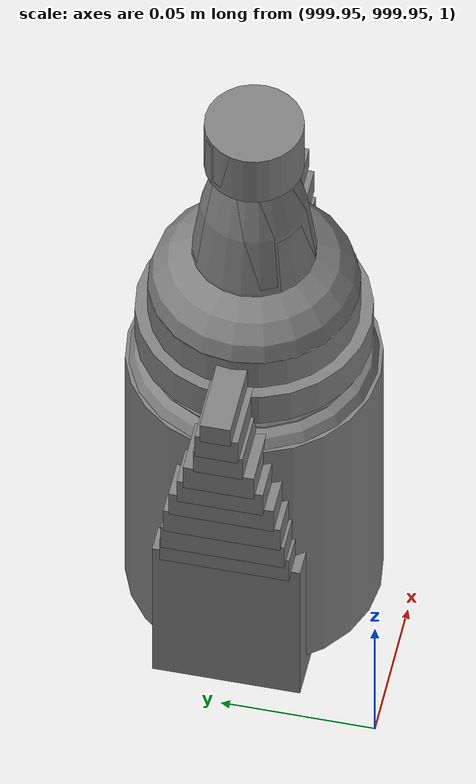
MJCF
<mujoco>
    <option gravity="0.000000000 0.000000000 -9.810000420" timestep="0.0166666" integrator="implicitfast" density="1.225" viscosity="1.8000001e-05" noslip_iterations="10" iterations="100" sdf_iterations="50">
        <flag multiccd="disable"/>
    </option>
    <size memory="1000M"/>
    <compiler coordinate="local"/>
    <worldbody>
        <light cutoff="30" pos="0 1 1" dir="0 -1 -2"/>
        <light cutoff="30" pos="0 -1 1" dir="0 1 -2"/>
        <body pos="-2.436573029 6.404376507 0.137849092" euler="0.000000000 0.000000000 0.000000000" name="openloong_gripper_2f85_fix_base_usda_shoppingtrolley_01">
            <geom contype="1" conaffinity="1" density="1000" type="box" material="" rgba="0.500000000 0.500000000 0.500000000 1.000000000" solimp="0.899999976 0.949999988 0.001000000" friction="1.000000000 0.005000000 0.000100000" solref="0.020000000 1.000000000" margin="0" condim="3" group="0" pos="-0.169898406 -0.178061336 0.864131629" quat="0.916343808 -0.400392294 -0.000000045 0.000000030" size="0.017999999 0.022499999 0.089999996" name="openloong_gripper_2f85_fix_base_usda_geom_C4AA448F_D844_461C_8EE9_7BBA85F7BDE4"/>
            <geom contype="1" conaffinity="1" density="1000" type="box" material="" rgba="0.500000000 0.500000000 0.500000000 1.000000000" solimp="0.899999976 0.949999988 0.001000000" friction="1.000000000 0.005000000 0.000100000" solref="0.020000000 1.000000000" margin="0" condim="3" group="0" pos="-0.107458733 0.238907143 0.911498845" quat="0.634576976 0.622505128 -0.330067992 -0.317575932" size="0.017999999 0.022499999 0.035999998" name="openloong_gripper_2f85_fix_base_usda_geom_7D7CD5BB_8E7E_4A07_8062_D1968D6D998B"/>
            <geom contype="1" conaffinity="1" density="1000" type="box" material="" rgba="0.500000000 0.500000000 0.500000000 1.000000000" solimp="0.899999976 0.949999988 0.001000000" friction="1.000000000 0.005000000 0.000100000" solref="0.020000000 1.000000000" margin="0" condim="3" group="0" pos="-0.005004787 0.248085022 0.912686050" quat="1.000000000 0.000000000 0.000000000 0.000000000" size="0.107999995 0.022499999 0.022499999" name="openloong_gripper_2f85_fix_base_usda_geom_8569C4CD_2535_4CDF_9D88_D99353A7445D"/>
            <geom contype="1" conaffinity="1" density="1000" type="box" material="" rgba="0.500000000 0.500000000 0.500000000 1.000000000" solimp="0.899999976 0.949999988 0.001000000" friction="1.000000000 0.005000000 0.000100000" solref="0.020000000 1.000000000" margin="0" condim="3" group="0" pos="0.131482959 -0.182533979 0.598989725" quat="0.996607125 0.055331629 0.059003670 0.015205893" size="0.013499999 0.287999988 0.053999998" name="openloong_gripper_2f85_fix_base_usda_geom_3FE8D800_640C_4504_B3D8_6D94D1EDBB63"/>
            <geom contype="1" conaffinity="1" density="1000" type="box" material="" rgba="0.500000000 0.500000000 0.500000000 1.000000000" solimp="0.899999976 0.949999988 0.001000000" friction="1.000000000 0.005000000 0.000100000" solref="0.020000000 1.000000000" margin="0" condim="3" group="0" pos="-0.000005364 0.100332208 0.734785020" quat="0.999668717 0.025737956 -0.000000010 0.000000000" size="0.135000005 0.019800000 0.152999997" name="openloong_gripper_2f85_fix_base_usda_geom_5FE5E415_FCA6_4463_88E2_EA18B491BB18"/>
            <geom contype="1" conaffinity="1" density="1000" type="box" material="" rgba="0.500000000 0.500000000 0.500000000 1.000000000" solimp="0.899999976 0.949999988 0.001000000" friction="1.000000000 0.005000000 0.000100000" solref="0.020000000 1.000000000" margin="0" condim="3" group="0" pos="-0.126757339 -0.182533979 0.598989725" quat="0.996607184 0.055331606 -0.059003651 -0.015205891" size="0.013499999 0.287999988 0.053999998" name="openloong_gripper_2f85_fix_base_usda_geom_82EE6E5C_3C61_4330_92D3_1C6A0051E464"/>
            <geom contype="1" conaffinity="1" density="1000" type="box" material="" rgba="0.500000000 0.500000000 0.500000000 1.000000000" solimp="0.899999976 0.949999988 0.001000000" friction="1.000000000 0.005000000 0.000100000" solref="0.020000000 1.000000000" margin="0" condim="3" group="0" pos="-0.134013891 0.200098798 0.912192523" quat="0.694057047 0.679413557 -0.172947660 -0.163618833" size="0.017999999 0.022499999 0.035999998" name="openloong_gripper_2f85_fix_base_usda_geom_D276DDA6_3C68_48C6_95BD_5977575C6F5F"/>
            <geom contype="1" conaffinity="1" density="1000" type="box" material="" rgba="0.500000000 0.500000000 0.500000000 1.000000000" solimp="0.899999976 0.949999988 0.001000000" friction="1.000000000 0.005000000 0.000100000" solref="0.020000000 1.000000000" margin="0" condim="3" group="0" pos="0.141839072 -0.191051379 0.702451229" quat="0.997147262 0.056065105 0.045779929 0.021407485" size="0.013499999 0.287999988 0.053999998" name="openloong_gripper_2f85_fix_base_usda_geom_62701C28_CA5B_47C7_A8E1_C11E022A8602"/>
            <geom contype="1" conaffinity="1" density="1000" type="box" material="" rgba="0.500000000 0.500000000 0.500000000 1.000000000" solimp="0.899999976 0.949999988 0.001000000" friction="1.000000000 0.005000000 0.000100000" solref="0.020000000 1.000000000" margin="0" condim="3" group="0" pos="-0.135714188 -0.191051379 0.694841146" quat="0.997147322 0.056064609 -0.045779683 -0.021407485" size="0.013499999 0.287999988 0.053999998" name="openloong_gripper_2f85_fix_base_usda_geom_0908835A_1D3B_4623_A9CF_0B64BA744CEC"/>
            <geom contype="1" conaffinity="1" density="1000" type="box" material="" rgba="0.500000000 0.500000000 0.500000000 1.000000000" solimp="0.899999976 0.949999988 0.001000000" friction="1.000000000 0.005000000 0.000100000" solref="0.020000000 1.000000000" margin="0" condim="3" group="0" pos="-0.000004721 -0.174527690 0.560063601" quat="0.996704638 0.081116498 -0.000000004 0.000000000" size="0.126000002 0.287999988 0.009000000" name="openloong_gripper_2f85_fix_base_usda_geom_8159A261_9145_4B11_A985_165D507F75E9"/>
            <geom contype="1" conaffinity="1" density="1000" type="box" material="" rgba="0.500000000 0.500000000 0.500000000 1.000000000" solimp="0.899999976 0.949999988 0.001000000" friction="1.000000000 0.005000000 0.000100000" solref="0.020000000 1.000000000" margin="0" condim="3" group="0" pos="0.134013891 0.200098798 0.912192523" quat="0.692574680 -0.680924535 -0.166899428 0.169783980" size="0.017999999 0.022499999 0.035999998" name="openloong_gripper_2f85_fix_base_usda_geom_4E094B32_E6C8_4ED3_ACE9_332E11CF86B4"/>
            <geom contype="1" conaffinity="1" density="1000" type="box" material="" rgba="0.500000000 0.500000000 0.500000000 1.000000000" solimp="0.899999976 0.949999988 0.001000000" friction="1.000000000 0.005000000 0.000100000" solref="0.020000000 1.000000000" margin="0" condim="3" group="0" pos="-0.012634277 -0.174527690 -0.088243507" quat="1.000000000 0.000000000 -0.000000004 0.000000000" size="0.135000005 0.287999988 0.044999998" name="openloong_gripper_2f85_fix_base_usda_geom_C0A34C02_AFD1_4109_8731_291C4740B1A3"/>
            <geom contype="1" conaffinity="1" density="1000" type="box" material="" rgba="0.500000000 0.500000000 0.500000000 1.000000000" solimp="0.899999976 0.949999988 0.001000000" friction="1.000000000 0.005000000 0.000100000" solref="0.020000000 1.000000000" margin="0" condim="3" group="0" pos="-0.142927840 -0.199506134 0.784674108" quat="0.998421252 0.016904408 -0.027109101 -0.046199299" size="0.013499999 0.305999994 0.063000001" name="openloong_gripper_2f85_fix_base_usda_geom_63A7D045_2539_454B_9706_A46A9ABA6487"/>
            <geom contype="1" conaffinity="1" density="1000" type="box" material="" rgba="0.500000000 0.500000000 0.500000000 1.000000000" solimp="0.899999976 0.949999988 0.001000000" friction="1.000000000 0.005000000 0.000100000" solref="0.020000000 1.000000000" margin="0" condim="3" group="0" pos="-0.169898406 -0.043119621 0.915120542" quat="0.687021017 0.726584017 -0.005590606 -0.006832919" size="0.017999999 0.022499999 0.089999996" name="openloong_gripper_2f85_fix_base_usda_geom_CB83137F_FC4E_4928_AD50_3393EC5A459F"/>
            <geom contype="1" conaffinity="1" density="1000" type="box" material="" rgba="0.500000000 0.500000000 0.500000000 1.000000000" solimp="0.899999976 0.949999988 0.001000000" friction="1.000000000 0.005000000 0.000100000" solref="0.020000000 1.000000000" margin="0" condim="3" group="0" pos="-0.000006008 -0.484932661 0.670727849" quat="0.997585475 0.069449045 -0.000000004 -0.000000089" size="0.179999992 0.013499999 0.170999989" name="openloong_gripper_2f85_fix_base_usda_geom_612FC235_4B27_462A_85DC_2FA434FDCB64"/>
            <geom contype="1" conaffinity="1" density="1000" type="box" material="" rgba="0.500000000 0.500000000 0.500000000 1.000000000" solimp="0.899999976 0.949999988 0.001000000" friction="1.000000000 0.005000000 0.000100000" solref="0.020000000 1.000000000" margin="0" condim="3" group="0" pos="0.160832971 0.103427693 0.910528183" quat="0.711112797 -0.700149298 -0.042821646 0.047705106" size="0.017999999 0.022499999 0.071999997" name="openloong_gripper_2f85_fix_base_usda_geom_243254D3_66E2_41D5_92C2_6B05003F935B"/>
            <geom contype="1" conaffinity="1" density="1000" type="box" material="" rgba="0.500000000 0.500000000 0.500000000 1.000000000" solimp="0.899999976 0.949999988 0.001000000" friction="1.000000000 0.005000000 0.000100000" solref="0.020000000 1.000000000" margin="0" condim="3" group="0" pos="-0.160832763 0.103427693 0.910528183" quat="0.711469591 0.699786782 -0.048386075 -0.042050660" size="0.017999999 0.022499999 0.071999997" name="openloong_gripper_2f85_fix_base_usda_geom_C3EEA7C8_02A5_487F_B0B5_B51CBD71400B"/>
            <geom contype="1" conaffinity="1" density="1000" type="box" material="" rgba="0.500000000 0.500000000 0.500000000 1.000000000" solimp="0.899999976 0.949999988 0.001000000" friction="1.000000000 0.005000000 0.000100000" solref="0.020000000 1.000000000" margin="0" condim="3" group="0" pos="0.169898629 -0.178061336 0.864131629" quat="0.916343808 -0.400392294 -0.000000045 0.000000030" size="0.017999999 0.022499999 0.089999996" name="openloong_gripper_2f85_fix_base_usda_geom_778638BF_D3EA_478A_9681_B0BA97F8AAD3"/>
            <geom contype="1" conaffinity="1" density="1000" type="box" material="" rgba="0.500000000 0.500000000 0.500000000 1.000000000" solimp="0.899999976 0.949999988 0.001000000" friction="1.000000000 0.005000000 0.000100000" solref="0.020000000 1.000000000" margin="0" condim="3" group="0" pos="0.103667587 0.233050480 0.912927270" quat="0.634205043 -0.622199059 -0.324503720 0.324576139" size="0.017999999 0.022499999 0.035999998" name="openloong_gripper_2f85_fix_base_usda_geom_776234D5_E671_4846_9024_4A581C1B9549"/>
            <geom contype="1" conaffinity="1" density="1000" type="box" material="" rgba="0.500000000 0.500000000 0.500000000 1.000000000" solimp="0.899999976 0.949999988 0.001000000" friction="1.000000000 0.005000000 0.000100000" solref="0.020000000 1.000000000" margin="0" condim="3" group="0" pos="0.169898629 -0.043119621 0.915120542" quat="0.687029123 -0.726576388 -0.006509603 0.005963952" size="0.017999999 0.022499999 0.089999996" name="openloong_gripper_2f85_fix_base_usda_geom_CFDEB2D6_D23B_4047_A511_048ECD085B67"/>
            <geom contype="1" conaffinity="1" density="1000" type="box" material="" rgba="0.500000000 0.500000000 0.500000000 1.000000000" solimp="0.899999976 0.949999988 0.001000000" friction="1.000000000 0.005000000 0.000100000" solref="0.020000000 1.000000000" margin="0" condim="3" group="0" pos="0.148195267 -0.199506566 0.782808602" quat="0.998808920 0.017156634 0.026950166 0.036880098" size="0.013499999 0.305999994 0.063000001" name="openloong_gripper_2f85_fix_base_usda_geom_0DD6DEF5_BFD3_4B5E_8D72_43661A250357"/>
            <freejoint name="openloong_gripper_2f85_fix_base_usda_shoppingtrolley_01_joint"/>
            <site size="0.005000000 0.005000000 0.005000000" rgba="0.500000000 0.500000000 0.500000000 1.000000000" pos="0.000000000 0.000000000 0.000000000" quat="1.000000000 0.000000000 0.000000000 0.000000000" group="0" type="sphere" name="openloong_gripper_2f85_fix_base_usda_shoppingtrolley_01"/>
        </body>
        <body pos="1000.000000000 1000.000000000 1.000000000" euler="0.000000000 0.000000000 0.000000000" name="openloong_gripper_2f85_fix_base_usda_jar_01">
            <geom contype="1" conaffinity="1" density="1000" type="box" material="" rgba="0.500000000 0.500000000 0.500000000 1.000000000" solimp="0.899999976 0.949999988 0.001000000" friction="1.000000000 0.005000000 0.000100000" solref="0.020000000 1.000000000" margin="0" condim="3" group="0" pos="0.000000000 0.000000000 0.006158113" quat="1.000000000 0.000000000 0.000000000 0.000000000" size="0.020000000 0.020000000 0.005000000" name="openloong_gripper_2f85_fix_base_usda_geom_7583E36E_2E67_4C37_8BFC_44DB9418AC4A"/>
            <geom contype="1" conaffinity="1" density="1000" type="cylinder" material="" rgba="0.500000000 0.500000000 0.500000000 1.000000000" solimp="0.899999976 0.949999988 0.001000000" friction="1.000000000 0.005000000 0.000100000" solref="0.020000000 1.000000000" margin="0" condim="3" group="0" pos="0.000000000 0.000000000 0.062744498" quat="1.000000000 0.000000000 0.000000000 0.000000000" size="0.041000001 0.052999999 1.000000000" name="openloong_gripper_2f85_fix_base_usda_geom_D75419F1_4306_4371_8CE6_DE47A491336F"/>
            <geom contype="1" conaffinity="1" density="1000" type="ellipsoid" material="" rgba="0.500000000 0.500000000 0.500000000 1.000000000" solimp="0.899999976 0.949999988 0.001000000" friction="1.000000000 0.005000000 0.000100000" solref="0.020000000 1.000000000" margin="0" condim="3" group="0" pos="0.000000000 0.000000000 0.122252703" quat="1.000000000 0.000000000 0.000000000 0.000000000" size="0.035999998 0.035999998 0.010000000" name="openloong_gripper_2f85_fix_base_usda_geom_14220FF6_9E50_4461_9209_0DA428647BF2"/>
            <geom contype="1" conaffinity="1" density="1000" type="cylinder" material="" rgba="0.500000000 0.500000000 0.500000000 1.000000000" solimp="0.899999976 0.949999988 0.001000000" friction="1.000000000 0.005000000 0.000100000" solref="0.020000000 1.000000000" margin="0" condim="3" group="0" pos="0.000000000 0.000000000 0.015747190" quat="1.000000000 0.000000000 0.000000000 0.000000000" size="0.035000000 0.010000000 1.000000000" name="openloong_gripper_2f85_fix_base_usda_geom_ED73D21A_D0D7_478A_B76F_E63DA8DF5F88"/>
            <geom contype="1" conaffinity="1" density="1000" type="ellipsoid" material="" rgba="0.500000000 0.500000000 0.500000000 1.000000000" solimp="0.899999976 0.949999988 0.001000000" friction="1.000000000 0.005000000 0.000100000" solref="0.020000000 1.000000000" margin="0" condim="3" group="0" pos="0.000000000 0.000000000 0.115815401" quat="1.000000000 0.000000000 0.000000000 0.000000000" size="0.039999999 0.039999999 0.010000000" name="openloong_gripper_2f85_fix_base_usda_geom_ACFF1FA8_7AD7_462C_B1F4_9E59F7BC34A4"/>
            <geom contype="1" conaffinity="1" density="1000" type="cylinder" material="" rgba="0.500000000 0.500000000 0.500000000 1.000000000" solimp="0.899999976 0.949999988 0.001000000" friction="1.000000000 0.005000000 0.000100000" solref="0.020000000 1.000000000" margin="0" condim="3" group="0" pos="0.000000000 0.000000000 0.133183479" quat="1.000000000 0.000000000 0.000000000 0.000000000" size="0.037999999 0.006500000 1.000000000" name="openloong_gripper_2f85_fix_base_usda_geom_D3443658_3693_4B42_AAF0_4A5F18B0594F"/>
            <freejoint name="openloong_gripper_2f85_fix_base_usda_jar_01_joint"/>
            <site size="0.005000000 0.005000000 0.005000000" rgba="0.500000000 0.500000000 0.500000000 1.000000000" pos="0.000000000 0.000000000 0.000000000" quat="1.000000000 0.000000000 0.000000000 0.000000000" group="0" type="sphere" name="openloong_gripper_2f85_fix_base_usda_jar_01site"/>
        </body>
        <body pos="-1.771967888 5.770671368 1.751487613" euler="-130.587005615 31.527280807 9.200949669" mocap="true" name="spotlight4_SpotLight"/>
        <body pos="1000.000000000 1000.000000000 1.000000000" euler="0.000000000 0.000000000 0.000000000" name="openloong_gripper_2f85_fix_base_usda_can">
            <geom contype="1" conaffinity="1" density="1000" type="cylinder" material="" rgba="0.500000000 0.500000000 0.500000000 1.000000000" solimp="0.899999976 0.949999988 0.001000000" friction="1.000000000 0.005000000 0.000100000" solref="0.020000000 1.000000000" margin="0" condim="3" group="0" pos="0.000000000 0.000000000 0.079676986" quat="1.000000000 0.000000000 0.000000000 0.000000000" size="0.034000002 0.071999997 1.000000000" name="openloong_gripper_2f85_fix_base_usda_geom_C77433C5_995B_417C_9B28_88D0BD8A8DC0"/>
            <geom contype="1" conaffinity="1" density="1000" type="ellipsoid" material="" rgba="0.500000000 0.500000000 0.500000000 1.000000000" solimp="0.899999976 0.949999988 0.001000000" friction="1.000000000 0.005000000 0.000100000" solref="0.020000000 1.000000000" margin="0" condim="3" group="0" pos="0.000000000 0.000000000 0.151854277" quat="1.000000000 0.000000000 0.000000000 0.000000000" size="0.034000002 0.034000002 0.020000000" name="openloong_gripper_2f85_fix_base_usda_geom_2929173D_E684_44A1_8D64_0AAF47EE6D02"/>
            <geom contype="1" conaffinity="1" density="1000" type="box" material="" rgba="0.500000000 0.500000000 0.500000000 1.000000000" solimp="0.899999976 0.949999988 0.001000000" friction="1.000000000 0.005000000 0.000100000" solref="0.020000000 1.000000000" margin="0" condim="3" group="0" pos="0.000000000 0.000000000 0.004777670" quat="1.000000000 0.000000000 0.000000000 0.000000000" size="0.020000000 0.020000000 0.005000000" name="openloong_gripper_2f85_fix_base_usda_geom_09DE1CCB_3877_451B_9B38_888F50CAE3DB"/>
            <freejoint name="openloong_gripper_2f85_fix_base_usda_can_joint"/>
            <site size="0.005000000 0.005000000 0.005000000" rgba="0.500000000 0.500000000 0.500000000 1.000000000" pos="0.000000000 0.000000000 0.000000000" quat="1.000000000 0.000000000 0.000000000 0.000000000" group="0" type="sphere" name="openloong_gripper_2f85_fix_base_usda_cansite"/>
        </body>
        <body pos="1000.000000000 1000.000000000 1.000000000" euler="0.000000000 0.000000000 0.000000000" name="openloong_gripper_2f85_fix_base_usda_salt">
            <geom contype="1" conaffinity="1" density="1000" type="box" material="" rgba="0.500000000 0.500000000 0.500000000 1.000000000" solimp="0.899999976 0.949999988 0.001000000" friction="1.000000000 0.005000000 0.000100000" solref="0.020000000 1.000000000" margin="0" condim="3" group="0" pos="0.000305176 0.000000000 0.084862232" quat="1.000000000 0.000000000 0.000000000 0.000000000" size="0.048999999 0.018999999 0.005000000" name="openloong_gripper_2f85_fix_base_usda_geom_E15D6B14_3CC8_443A_AC3D_534D021809A8"/>
            <geom contype="1" conaffinity="1" density="1000" type="box" material="" rgba="0.500000000 0.500000000 0.500000000 1.000000000" solimp="0.899999976 0.949999988 0.001000000" friction="1.000000000 0.005000000 0.000100000" solref="0.020000000 1.000000000" margin="0" condim="3" group="0" pos="0.000305176 0.000000000 0.104564309" quat="1.000000000 0.000000000 0.000000000 0.000000000" size="0.052000001 0.014000000 0.005000000" name="openloong_gripper_2f85_fix_base_usda_geom_45FC2F9C_615C_4F72_B26E_3FDAE31F4AF4"/>
            <geom contype="1" conaffinity="1" density="1000" type="box" material="" rgba="0.500000000 0.500000000 0.500000000 1.000000000" solimp="0.899999976 0.949999988 0.001000000" friction="1.000000000 0.005000000 0.000100000" solref="0.020000000 1.000000000" margin="0" condim="3" group="0" pos="0.000305176 0.000000000 0.114487171" quat="1.000000000 0.000000000 0.000000000 0.000000000" size="0.054000001 0.011500000 0.005000000" name="openloong_gripper_2f85_fix_base_usda_geom_729EC259_90B7_4F7C_A540_01713013E824"/>
            <geom contype="1" conaffinity="1" density="1000" type="box" material="" rgba="0.500000000 0.500000000 0.500000000 1.000000000" solimp="0.899999976 0.949999988 0.001000000" friction="1.000000000 0.005000000 0.000100000" solref="0.020000000 1.000000000" margin="0" condim="3" group="0" pos="0.000305176 0.000000000 0.075103164" quat="1.000000000 0.000000000 0.000000000 0.000000000" size="0.048000000 0.020000000 0.005000000" name="openloong_gripper_2f85_fix_base_usda_geom_DD906AF7_B9E1_4C96_ACE8_FDA371E7B318"/>
            <geom contype="1" conaffinity="1" density="1000" type="box" material="" rgba="0.500000000 0.500000000 0.500000000 1.000000000" solimp="0.899999976 0.949999988 0.001000000" friction="1.000000000 0.005000000 0.000100000" solref="0.020000000 1.000000000" margin="0" condim="3" group="0" pos="0.000305176 0.000000000 0.134892464" quat="1.000000000 0.000000000 0.000000000 0.000000000" size="0.057000000 0.007000000 0.005000000" name="openloong_gripper_2f85_fix_base_usda_geom_2C376F7D_9BF0_41ED_A284_1A2C135284E7"/>
            <geom contype="1" conaffinity="1" density="1000" type="box" material="" rgba="0.500000000 0.500000000 0.500000000 1.000000000" solimp="0.899999976 0.949999988 0.001000000" friction="1.000000000 0.005000000 0.000100000" solref="0.020000000 1.000000000" margin="0" condim="3" group="0" pos="0.000305176 0.000000000 0.094920278" quat="1.000000000 0.000000000 0.000000000 0.000000000" size="0.050000001 0.017000001 0.005000000" name="openloong_gripper_2f85_fix_base_usda_geom_9B170AA5_3924_48D5_B983_6CEF854CCADF"/>
            <geom contype="1" conaffinity="1" density="1000" type="box" material="" rgba="0.500000000 0.500000000 0.500000000 1.000000000" solimp="0.899999976 0.949999988 0.001000000" friction="1.000000000 0.005000000 0.000100000" solref="0.020000000 1.000000000" margin="0" condim="3" group="0" pos="0.000305176 0.000000000 0.065204859" quat="1.000000000 0.000000000 0.000000000 0.000000000" size="0.045000002 0.021000000 0.005000000" name="openloong_gripper_2f85_fix_base_usda_geom_A6E0C756_7F99_424E_932B_CAB9156A2D4F"/>
            <geom contype="1" conaffinity="1" density="1000" type="box" material="" rgba="0.500000000 0.500000000 0.500000000 1.000000000" solimp="0.899999976 0.949999988 0.001000000" friction="1.000000000 0.005000000 0.000100000" solref="0.020000000 1.000000000" margin="0" condim="3" group="0" pos="0.000305176 0.000000000 0.144135714" quat="1.000000000 0.000000000 0.000000000 0.000000000" size="0.059000000 0.005000000 0.004000000" name="openloong_gripper_2f85_fix_base_usda_geom_60A10312_9362_44D0_93FF_0B7B1BD17FD3"/>
            <geom contype="1" conaffinity="1" density="1000" type="box" material="" rgba="0.500000000 0.500000000 0.500000000 1.000000000" solimp="0.899999976 0.949999988 0.001000000" friction="1.000000000 0.005000000 0.000100000" solref="0.020000000 1.000000000" margin="0" condim="3" group="0" pos="0.000000000 0.000000000 0.031593561" quat="1.000000000 0.000000000 0.000000000 0.000000000" size="0.041999999 0.024000000 0.029999999" name="openloong_gripper_2f85_fix_base_usda_geom_E92CB941_BFA7_4536_9DB7_AACD0581FC38"/>
            <geom contype="1" conaffinity="1" density="1000" type="box" material="" rgba="0.500000000 0.500000000 0.500000000 1.000000000" solimp="0.899999976 0.949999988 0.001000000" friction="1.000000000 0.005000000 0.000100000" solref="0.020000000 1.000000000" margin="0" condim="3" group="0" pos="0.000305176 0.000000000 0.124608755" quat="1.000000000 0.000000000 0.000000000 0.000000000" size="0.055000000 0.008000000 0.005000000" name="openloong_gripper_2f85_fix_base_usda_geom_E13EFC54_EE21_48C5_9E01_0735F5F11611"/>
            <freejoint name="openloong_gripper_2f85_fix_base_usda_salt_joint"/>
            <site size="0.005000000 0.005000000 0.005000000" rgba="0.500000000 0.500000000 0.500000000 1.000000000" pos="0.000000000 0.000000000 0.000000000" quat="1.000000000 0.000000000 0.000000000 0.000000000" group="0" type="sphere" name="openloong_gripper_2f85_fix_base_usda_saltsite"/>
        </body>
        <body pos="1000.000000000 1000.000000000 1.000000000" euler="0.000000000 0.000000000 0.000000000" name="openloong_gripper_2f85_fix_base_usda_bottle_red">
            <geom contype="1" conaffinity="1" density="1000" type="ellipsoid" material="" rgba="0.500000000 0.500000000 0.500000000 1.000000000" solimp="0.899999976 0.949999988 0.001000000" friction="1.000000000 0.005000000 0.000100000" solref="0.020000000 1.000000000" margin="0" condim="3" group="0" pos="0.000000000 0.000000000 0.144284487" quat="1.000000000 0.000000000 0.000000000 0.000000000" size="0.021000000 0.021000000 0.079999998" name="openloong_gripper_2f85_fix_base_usda_geom_9C63AD8E_1C21_4776_B3D2_81B22DD9B77F"/>
            <geom contype="1" conaffinity="1" density="1000" type="cylinder" material="" rgba="0.500000000 0.500000000 0.500000000 1.000000000" solimp="0.899999976 0.949999988 0.001000000" friction="1.000000000 0.005000000 0.000100000" solref="0.020000000 1.000000000" margin="0" condim="3" group="0" pos="0.000000000 0.000000000 0.220618963" quat="1.000000000 0.000000000 0.000000000 0.000000000" size="0.016000001 0.010000000 1.000000000" name="openloong_gripper_2f85_fix_base_usda_geom_61FE75AC_CB18_4959_B9FE_E9D84C95060A"/>
            <geom contype="1" conaffinity="1" density="1000" type="ellipsoid" material="" rgba="0.500000000 0.500000000 0.500000000 1.000000000" solimp="0.899999976 0.949999988 0.001000000" friction="1.000000000 0.005000000 0.000100000" solref="0.020000000 1.000000000" margin="0" condim="3" group="0" pos="0.000000000 0.000000000 0.118945479" quat="1.000000000 0.000000000 0.000000000 0.000000000" size="0.030999999 0.030999999 0.029999999" name="openloong_gripper_2f85_fix_base_usda_geom_46DA6D88_4390_4596_85BD_74EFF587F183"/>
            <geom contype="1" conaffinity="1" density="1000" type="box" material="" rgba="0.500000000 0.500000000 0.500000000 1.000000000" solimp="0.899999976 0.949999988 0.001000000" friction="1.000000000 0.005000000 0.000100000" solref="0.020000000 1.000000000" margin="0" condim="3" group="0" pos="0.000000000 0.000000000 0.002189159" quat="1.000000000 0.000000000 0.000000000 0.000000000" size="0.020000000 0.020000000 0.003000000" name="openloong_gripper_2f85_fix_base_usda_geom_D01217AB_8C62_4F5F_9D85_78000AEB8BB4"/>
            <geom contype="1" conaffinity="1" density="1000" type="cylinder" material="" rgba="0.500000000 0.500000000 0.500000000 1.000000000" solimp="0.899999976 0.949999988 0.001000000" friction="1.000000000 0.005000000 0.000100000" solref="0.020000000 1.000000000" margin="0" condim="3" group="0" pos="0.000000000 -0.000366211 0.060884237" quat="1.000000000 0.000000000 0.000000000 0.000000000" size="0.030999999 0.057999998 1.000000000" name="openloong_gripper_2f85_fix_base_usda_geom_12D1784A_B15C_4F51_9EB2_CB26FA5B1ECD"/>
            <freejoint name="openloong_gripper_2f85_fix_base_usda_bottle_red_joint"/>
            <site size="0.005000000 0.005000000 0.005000000" rgba="0.500000000 0.500000000 0.500000000 1.000000000" pos="0.000000000 0.000000000 0.000000000" quat="0.999961913 0.008726535 0.000000000 0.000000000" group="0" type="sphere" name="openloong_gripper_2f85_fix_base_usda_bottle_redsite"/>
        </body>
        <body pos="-1.843620777 5.739521503 1.711071610" euler="22.898801804 -52.558803558 -13.349474907" mocap="true" name="spotlight6_SpotLight"/>
        <body pos="1000.000000000 1000.000000000 1.000000000" euler="0.000000000 0.000000000 0.000000000" name="openloong_gripper_2f85_fix_base_usda_bottle_blue">
            <geom contype="1" conaffinity="1" density="1000" type="ellipsoid" material="" rgba="0.500000000 0.500000000 0.500000000 1.000000000" solimp="0.899999976 0.949999988 0.001000000" friction="1.000000000 0.005000000 0.000100000" solref="0.020000000 1.000000000" margin="0" condim="3" group="0" pos="0.000000000 0.000000000 0.118920922" quat="1.000000000 0.000000000 0.000000000 0.000000000" size="0.030999999 0.030999999 0.029999999" name="openloong_gripper_2f85_fix_base_usda_geom_234C9BC8_5AEB_4771_B999_EA060C11434E"/>
            <geom contype="1" conaffinity="1" density="1000" type="box" material="" rgba="0.500000000 0.500000000 0.500000000 1.000000000" solimp="0.899999976 0.949999988 0.001000000" friction="1.000000000 0.005000000 0.000100000" solref="0.020000000 1.000000000" margin="0" condim="3" group="0" pos="0.000000000 0.000000000 0.002164602" quat="1.000000000 0.000000000 0.000000000 0.000000000" size="0.020000000 0.020000000 0.003000000" name="openloong_gripper_2f85_fix_base_usda_geom_CE60C631_635B_4225_985C_8FCC8C0F23F1"/>
            <geom contype="1" conaffinity="1" density="1000" type="cylinder" material="" rgba="0.500000000 0.500000000 0.500000000 1.000000000" solimp="0.899999976 0.949999988 0.001000000" friction="1.000000000 0.005000000 0.000100000" solref="0.020000000 1.000000000" margin="0" condim="3" group="0" pos="0.000000000 -0.000366211 0.060859680" quat="1.000000000 0.000000000 0.000000000 0.000000000" size="0.030999999 0.057999998 1.000000000" name="openloong_gripper_2f85_fix_base_usda_geom_2094F89C_4DD1_4D8D_B0B7_5F4310B1B577"/>
            <geom contype="1" conaffinity="1" density="1000" type="cylinder" material="" rgba="0.500000000 0.500000000 0.500000000 1.000000000" solimp="0.899999976 0.949999988 0.001000000" friction="1.000000000 0.005000000 0.000100000" solref="0.020000000 1.000000000" margin="0" condim="3" group="0" pos="0.000000000 0.000000000 0.220594406" quat="1.000000000 0.000000000 0.000000000 0.000000000" size="0.016000001 0.010000000 1.000000000" name="openloong_gripper_2f85_fix_base_usda_geom_45C362BD_E1C1_41AF_B5C1_F7DD8A056DA7"/>
            <geom contype="1" conaffinity="1" density="1000" type="ellipsoid" material="" rgba="0.500000000 0.500000000 0.500000000 1.000000000" solimp="0.899999976 0.949999988 0.001000000" friction="1.000000000 0.005000000 0.000100000" solref="0.020000000 1.000000000" margin="0" condim="3" group="0" pos="0.000000000 0.000000000 0.144259930" quat="1.000000000 0.000000000 0.000000000 0.000000000" size="0.021000000 0.021000000 0.079999998" name="openloong_gripper_2f85_fix_base_usda_geom_2C2FB8C5_FBC6_444E_B249_801AA20C4409"/>
            <freejoint name="openloong_gripper_2f85_fix_base_usda_bottle_blue_joint"/>
            <site size="0.005000000 0.005000000 0.005000000" rgba="0.500000000 0.500000000 0.500000000 1.000000000" pos="0.000000000 0.000000000 0.000000000" quat="0.999961913 0.008726535 0.000000000 0.000000000" group="0" type="sphere" name="openloong_gripper_2f85_fix_base_usda_bottle_bluesite"/>
        </body>
        <body pos="-2.247532368 6.118879318 1.794467688" euler="-176.612930298 -20.691186905 -63.930698395" mocap="true" name="spotlight5_SpotLight"/>
        <body pos="0.000000000 0.000000000 0.000000000" euler="0.000000000 0.000000000 0.000000000" name=" Static Objects_ Static Objects">
            <geom contype="1" conaffinity="1" density="1000" type="box" material="" rgba="0.500000000 0.500000000 0.500000000 1.000000000" solimp="0.899999976 0.949999988 0.001000000" friction="1.000000000 0.005000000 0.000100000" solref="0.020000000 1.000000000" margin="0" condim="3" group="0" pos="-3.101639986 6.150595188 1.018643856" quat="1.000000000 0.000000000 0.000000000 0.000000000" size="0.050000001 0.579999983 1.019999981" name=" Static Objects_geom_E17468ED_0E79_49FE_BB4C_DC68CC2DE8D2"/>
            <geom contype="1" conaffinity="1" density="1000" type="box" material="" rgba="0.500000000 0.500000000 0.500000000 1.000000000" solimp="0.899999976 0.949999988 0.001000000" friction="1.000000000 0.005000000 0.000100000" solref="0.020000000 1.000000000" margin="0" condim="3" group="0" pos="-2.825197220 6.153595448 1.115278244" quat="0.707107067 0.000000000 0.000000000 0.707106471" size="0.550000012 0.239999995 0.025000000" name=" Static Objects_geom_1B032413_7CA7_4F18_B1DE_FC713FB800C6"/>
            <geom contype="1" conaffinity="1" density="1000" type="box" material="" rgba="0.500000000 0.500000000 0.500000000 1.000000000" solimp="0.899999976 0.949999988 0.001000000" friction="1.000000000 0.005000000 0.000100000" solref="0.020000000 1.000000000" margin="0" condim="3" group="0" pos="-2.825197220 6.153595448 0.097434282" quat="0.707107067 0.000000000 0.000000000 0.707106471" size="0.550000012 0.239999995 0.098999999" name=" Static Objects_geom_5152E158_A277_4309_B4E1_7E6D205221A5"/>
            <geom contype="1" conaffinity="1" density="1000" type="box" material="" rgba="0.500000000 0.500000000 0.500000000 1.000000000" solimp="0.899999976 0.949999988 0.001000000" friction="1.000000000 0.005000000 0.000100000" solref="0.020000000 1.000000000" margin="0" condim="3" group="0" pos="-6.293097973 6.153595448 1.114443064" quat="0.707107067 0.000000000 0.000000000 0.707106471" size="0.529999971 3.134999990 0.025000000" name=" Static Objects_geom_345575DD_B8D7_4747_80B7_25F8CF8BE025"/>
            <geom contype="1" conaffinity="1" density="1000" type="box" material="" rgba="0.500000000 0.500000000 0.500000000 1.000000000" solimp="0.899999976 0.949999988 0.001000000" friction="1.000000000 0.005000000 0.000100000" solref="0.020000000 1.000000000" margin="0" condim="3" group="0" pos="-6.286010742 6.153595448 0.096129179" quat="0.707107067 0.000000000 0.000000000 0.707106471" size="0.529999971 3.134999990 0.098999999" name=" Static Objects_geom_39C2B007_4AA8_45D0_B07D_44D22BE6E550"/>
            <geom contype="1" conaffinity="1" density="1000" type="box" material="" rgba="0.500000000 0.500000000 0.500000000 1.000000000" solimp="0.899999976 0.949999988 0.001000000" friction="1.000000000 0.005000000 0.000100000" solref="0.020000000 1.000000000" margin="0" condim="3" group="0" pos="-2.825197220 6.153595448 1.563861728" quat="0.707107067 0.000000000 0.000000000 0.707106471" size="0.550000012 0.239999995 0.025000000" name=" Static Objects_geom_ABE273EC_9A13_48A6_83F9_80B9831360ED"/>
            <geom contype="1" conaffinity="1" density="1000" type="box" material="" rgba="0.500000000 0.500000000 0.500000000 1.000000000" solimp="0.899999976 0.949999988 0.001000000" friction="1.000000000 0.005000000 0.000100000" solref="0.020000000 1.000000000" margin="0" condim="3" group="0" pos="-6.311686516 6.153595448 1.018643856" quat="0.707107067 0.000000000 0.000000000 0.707106471" size="0.050000001 3.150000095 1.019999981" name=" Static Objects_geom_B8BD0D92_348B_44EE_9E5E_E1FD8D573AD8"/>
            <geom contype="1" conaffinity="1" density="1000" type="box" material="" rgba="0.500000000 0.500000000 0.500000000 1.000000000" solimp="0.899999976 0.949999988 0.001000000" friction="1.000000000 0.005000000 0.000100000" solref="0.020000000 1.000000000" margin="0" condim="3" group="0" pos="-2.825197220 6.153595448 0.629031777" quat="0.707107067 0.000000000 0.000000000 0.707106471" size="0.550000012 0.239999995 0.025000000" name=" Static Objects_geom_7C980650_7360_4290_9DE3_D69B1D42BB3E"/>
            <geom contype="1" conaffinity="1" density="1000" type="box" material="" rgba="0.500000000 0.500000000 0.500000000 1.000000000" solimp="0.899999976 0.949999988 0.001000000" friction="1.000000000 0.005000000 0.000100000" solref="0.020000000 1.000000000" margin="0" condim="3" group="0" pos="-6.286010742 6.153595448 1.563861728" quat="0.707107067 0.000000000 0.000000000 0.707106471" size="0.529999971 3.134999990 0.025000000" name=" Static Objects_geom_495D3AB4_6D96_4276_B8A9_C3497C91F520"/>
            <geom contype="1" conaffinity="1" density="1000" type="box" material="" rgba="0.500000000 0.500000000 0.500000000 1.000000000" solimp="0.899999976 0.949999988 0.001000000" friction="1.000000000 0.005000000 0.000100000" solref="0.020000000 1.000000000" margin="0" condim="3" group="0" pos="-6.286010742 6.153595448 0.629031777" quat="0.707107067 0.000000000 0.000000000 0.707106471" size="0.529999971 3.134999990 0.025000000" name=" Static Objects_geom_19E23AC2_024C_4BCB_AA3F_14BDFD2DDC14"/>
            <geom contype="1" conaffinity="1" density="1000" type="box" material="" rgba="0.500000000 0.500000000 0.500000000 1.000000000" solimp="0.899999976 0.949999988 0.001000000" friction="1.000000000 0.005000000 0.000100000" solref="0.020000000 1.000000000" margin="0" condim="3" group="0" pos="-7.719123363 2.867671013 1.173410416" quat="1.000000000 0.000000000 0.000000000 0.000000000" size="0.250000000 0.250000000 0.079999998" name=" Static Objects_geom_D7D44258_FCBE_4CD2_967C_42CE1F7E3408"/>
            <geom contype="1" conaffinity="1" density="1000" type="box" material="" rgba="0.500000000 0.500000000 0.500000000 1.000000000" solimp="0.899999976 0.949999988 0.001000000" friction="1.000000000 0.005000000 0.000100000" solref="0.020000000 1.000000000" margin="0" condim="3" group="0" pos="-7.408766270 3.088089943 1.776644945" quat="0.928051054 0.000000000 0.000000000 0.372453064" size="0.050000001 0.100000001 0.050000001" name=" Static Objects_geom_EB6CE6CC_4058_4B72_8D5C_C424229B78CC"/>
            <geom contype="1" conaffinity="1" density="1000" type="box" material="" rgba="0.500000000 0.500000000 0.500000000 1.000000000" solimp="0.899999976 0.949999988 0.001000000" friction="1.000000000 0.005000000 0.000100000" solref="0.020000000 1.000000000" margin="0" condim="3" group="0" pos="-7.719123363 2.958004713 1.530241251" quat="1.000000000 0.000000000 0.000000000 0.000000000" size="0.250000000 0.159999996 0.280000001" name=" Static Objects_geom_64586887_1414_4765_99C4_B9CDD439C91B"/>
            <geom contype="1" conaffinity="1" density="1000" type="cylinder" material="" rgba="0.500000000 0.500000000 0.500000000 1.000000000" solimp="0.899999976 0.949999988 0.001000000" friction="1.000000000 0.005000000 0.000100000" solref="0.020000000 1.000000000" margin="0" condim="3" group="0" pos="-7.427312374 3.069516420 1.502544641" quat="0.928051054 0.000000000 0.000000000 0.372453064" size="0.015000000 0.230000004 0.100000001" name=" Static Objects_geom_2FCF2450_BCE2_4C2E_A6A3_62D7E0518317"/>
            <geom contype="1" conaffinity="1" density="1000" type="box" material="" rgba="0.500000000 0.500000000 0.500000000 1.000000000" solimp="0.899999976 0.949999988 0.001000000" friction="1.000000000 0.005000000 0.000100000" solref="0.020000000 1.000000000" margin="0" condim="3" group="0" pos="-7.437745571 3.067511320 1.289965630" quat="1.000000000 0.000000000 0.000000000 0.000000000" size="0.029999999 0.020000000 0.020000000" name=" Static Objects_geom_77A01F57_A739_4366_928F_572B86DF2CDD"/>
            <geom contype="1" conaffinity="1" density="1000" type="box" material="" rgba="0.500000000 0.500000000 0.500000000 1.000000000" solimp="0.899999976 0.949999988 0.001000000" friction="1.000000000 0.005000000 0.000100000" solref="0.020000000 1.000000000" margin="0" condim="3" group="0" pos="-9.058088303 6.434794426 1.209077358" quat="1.000000000 0.000000000 0.000000000 0.000000000" size="0.250000000 0.100000001 0.070000000" name=" Static Objects_geom_E0BA5F08_FA12_4E71_A43E_3C0AEC62692A"/>
            <geom contype="1" conaffinity="1" density="1000" type="box" material="" rgba="0.500000000 0.500000000 0.500000000 1.000000000" solimp="0.899999976 0.949999988 0.001000000" friction="1.000000000 0.005000000 0.000100000" solref="0.020000000 1.000000000" margin="0" condim="3" group="0" pos="-7.886891365 6.459744930 0.352518857" quat="1.000000000 0.000000000 0.000000000 0.000000000" size="1.500000000 0.200000003 0.150000006" name=" Static Objects_geom_A684B9D9_65F8_472A_B238_24FB6B4B2B9B"/>
            <geom contype="1" conaffinity="1" density="1000" type="box" material="" rgba="0.500000000 0.500000000 0.500000000 1.000000000" solimp="0.899999976 0.949999988 0.001000000" friction="1.000000000 0.005000000 0.000100000" solref="0.020000000 1.000000000" margin="0" condim="3" group="0" pos="-9.237723351 6.464855671 1.209077358" quat="1.000000000 0.000000000 0.000000000 0.000000000" size="0.100000001 0.100000001 0.070000000" name=" Static Objects_geom_1A053BF8_0692_4D44_9511_4C77246C4B18"/>
            <geom contype="1" conaffinity="1" density="1000" type="box" material="" rgba="0.500000000 0.500000000 0.500000000 1.000000000" solimp="0.899999976 0.949999988 0.001000000" friction="1.000000000 0.005000000 0.000100000" solref="0.020000000 1.000000000" margin="0" condim="3" group="0" pos="-6.924745083 6.362090111 1.214329123" quat="1.000000000 0.000000000 0.000000000 0.000000000" size="0.200000003 0.100000001 0.075000003" name=" Static Objects_geom_D5E0FC83_078E_45F0_AEBD_5E6D237D9CCF"/>
            <geom contype="1" conaffinity="1" density="1000" type="box" material="" rgba="0.500000000 0.500000000 0.500000000 1.000000000" solimp="0.899999976 0.949999988 0.001000000" friction="1.000000000 0.005000000 0.000100000" solref="0.020000000 1.000000000" margin="0" condim="3" group="0" pos="-4.407354832 6.459744930 1.292199373" quat="1.000000000 0.000000000 0.000000000 0.000000000" size="1.240000010 0.200000003 0.150000006" name=" Static Objects_geom_EB5DC7B1_DEE6_4F85_8B77_1918CD56CE40"/>
            <geom contype="1" conaffinity="1" density="1000" type="box" material="" rgba="0.500000000 0.500000000 0.500000000 1.000000000" solimp="0.899999976 0.949999988 0.001000000" friction="1.000000000 0.005000000 0.000100000" solref="0.020000000 1.000000000" margin="0" condim="3" group="0" pos="-5.611940861 6.318420410 0.350975692" quat="1.000000000 0.000000000 0.000000000 0.000000000" size="0.699999988 0.100000001 0.150000006" name=" Static Objects_geom_DE97EFA2_2F41_4DE5_87A0_F3AB029F5D28"/>
            <geom contype="1" conaffinity="1" density="1000" type="box" material="" rgba="0.500000000 0.500000000 0.500000000 1.000000000" solimp="0.899999976 0.949999988 0.001000000" friction="1.000000000 0.005000000 0.000100000" solref="0.020000000 1.000000000" margin="0" condim="3" group="0" pos="-6.300771236 6.459744930 1.744376063" quat="1.000000000 0.000000000 0.000000000 0.000000000" size="3.000000000 0.200000003 0.150000006" name=" Static Objects_geom_E8113403_3378_4B3D_B480_CF65144343B7"/>
            <geom contype="1" conaffinity="1" density="1000" type="box" material="" rgba="0.500000000 0.500000000 0.500000000 1.000000000" solimp="0.899999976 0.949999988 0.001000000" friction="1.000000000 0.005000000 0.000100000" solref="0.020000000 1.000000000" margin="0" condim="3" group="0" pos="-6.751636982 6.459744930 0.800981164" quat="1.000000000 0.000000000 0.000000000 0.000000000" size="2.200000048 0.200000003 0.150000006" name=" Static Objects_geom_2AE6DC47_3ACF_4AD7_9619_3CB3F2D583FE"/>
            <geom contype="1" conaffinity="1" density="1000" type="box" material="" rgba="0.500000000 0.500000000 0.500000000 1.000000000" solimp="0.899999976 0.949999988 0.001000000" friction="1.000000000 0.005000000 0.000100000" solref="0.020000000 1.000000000" margin="0" condim="3" group="0" pos="-8.844120979 6.464855671 1.209077358" quat="1.000000000 0.000000000 0.000000000 0.000000000" size="0.100000001 0.100000001 0.070000000" name=" Static Objects_geom_12930837_F94A_470C_A303_7596565E5B46"/>
            <geom contype="1" conaffinity="1" density="1000" type="box" material="" rgba="0.500000000 0.500000000 0.500000000 1.000000000" solimp="0.899999976 0.949999988 0.001000000" friction="1.000000000 0.005000000 0.000100000" solref="0.020000000 1.000000000" margin="0" condim="3" group="0" pos="-6.098561764 6.327973843 1.292199373" quat="1.000000000 0.000000000 0.000000000 0.000000000" size="0.500000000 0.100000001 0.150000006" name=" Static Objects_geom_AD6614DC_D5FF_4A80_BAB5_24DEBCFB77A1"/>
            <geom contype="1" conaffinity="1" density="1000" type="box" material="" rgba="0.500000000 0.500000000 0.500000000 1.000000000" solimp="0.899999976 0.949999988 0.001000000" friction="1.000000000 0.005000000 0.000100000" solref="0.020000000 1.000000000" margin="0" condim="3" group="0" pos="-6.824534416 6.447464466 1.212718010" quat="1.000000000 0.000000000 0.000000000 0.000000000" size="0.100000001 0.100000001 0.075000003" name=" Static Objects_geom_0AD7D1BB_33EA_4D59_9CA2_74230367DBD8"/>
            <geom contype="1" conaffinity="1" density="1000" type="box" material="" rgba="0.500000000 0.500000000 0.500000000 1.000000000" solimp="0.899999976 0.949999988 0.001000000" friction="1.000000000 0.005000000 0.000100000" solref="0.020000000 1.000000000" margin="0" condim="3" group="0" pos="-3.907610416 6.318625927 0.800981164" quat="1.000000000 0.000000000 0.000000000 0.000000000" size="0.500000000 0.100000001 0.150000006" name=" Static Objects_geom_81CCF7DE_96D0_4880_8988_F137D2DB3D20"/>
            <geom contype="1" conaffinity="1" density="1000" type="box" material="" rgba="0.500000000 0.500000000 0.500000000 1.000000000" solimp="0.899999976 0.949999988 0.001000000" friction="1.000000000 0.005000000 0.000100000" solref="0.020000000 1.000000000" margin="0" condim="3" group="0" pos="-7.373087406 6.458900928 1.214329123" quat="1.000000000 0.000000000 0.000000000 0.000000000" size="0.250000000 0.200000003 0.075000003" name=" Static Objects_geom_0D1C1746_DC7A_4E3E_BA07_21CF4C2CDA6A"/>
            <geom contype="1" conaffinity="1" density="1000" type="box" material="" rgba="0.500000000 0.500000000 0.500000000 1.000000000" solimp="0.899999976 0.949999988 0.001000000" friction="1.000000000 0.005000000 0.000100000" solref="0.020000000 1.000000000" margin="0" condim="3" group="0" pos="-4.035642624 6.459744930 0.352518857" quat="1.000000000 0.000000000 0.000000000 0.000000000" size="0.800000012 0.200000003 0.150000006" name=" Static Objects_geom_A4D2EEB2_B373_49D5_A4AE_65546041FF4C"/>
            <geom contype="1" conaffinity="1" density="1000" type="box" material="" rgba="0.500000000 0.500000000 0.500000000 1.000000000" solimp="0.899999976 0.949999988 0.001000000" friction="1.000000000 0.005000000 0.000100000" solref="0.020000000 1.000000000" margin="0" condim="3" group="0" pos="-6.460197449 2.937205315 0.548931718" quat="1.000000000 0.000000000 0.000000000 0.000000000" size="2.650000095 0.430000007 0.550000012" name=" Static Objects_geom_F70646C3_CEA5_4C4A_B4B4_4263130528AE"/>
            <geom contype="1" conaffinity="1" density="1000" type="box" material="" rgba="0.500000000 0.500000000 0.500000000 1.000000000" solimp="0.899999976 0.949999988 0.001000000" friction="1.000000000 0.005000000 0.000100000" solref="0.020000000 1.000000000" margin="0" condim="3" group="0" pos="-4.240264893 1.327049494 0.549888909" quat="1.000000000 0.000000000 0.000000000 0.000000000" size="0.430000007 1.200000048 0.550000012" name=" Static Objects_geom_9F220947_0183_423C_BD38_0EC9BC505B7D"/>
            <geom contype="1" conaffinity="1" density="1000" type="box" material="" rgba="0.500000000 0.500000000 0.500000000 1.000000000" solimp="0.899999976 0.949999988 0.001000000" friction="1.000000000 0.005000000 0.000100000" solref="0.020000000 1.000000000" margin="0" condim="3" group="0" pos="-8.830721855 2.096410990 0.549305558" quat="1.000000000 0.000000000 0.000000000 0.000000000" size="0.280000001 0.430000007 0.550000012" name=" Static Objects_geom_55CD43D7_E63D_4650_AB07_E189476CEAE8"/>
            <geom contype="1" conaffinity="1" density="1000" type="plane" material="" rgba="0.500000000 0.500000000 0.500000000 1.000000000" solimp="0.899999976 0.949999988 0.001000000" friction="1.000000000 0.005000000 0.000100000" solref="0.020000000 1.000000000" margin="0" condim="3" group="0" pos="-6.000000000 10.399999619 0.000000000" quat="1.000000000 0.000000000 0.000000000 0.000000000" size="6.050000191 10.800000191 0.010000000" name=" Static Objects_geom_32D952AB_A285_4010_8A2B_7DC983B88001"/>
            <geom contype="1" conaffinity="1" density="1000" type="box" material="" rgba="0.500000000 0.500000000 0.500000000 1.000000000" solimp="0.899999976 0.949999988 0.001000000" friction="1.000000000 0.005000000 0.000100000" solref="0.020000000 1.000000000" margin="0" condim="3" group="0" pos="-6.000000000 0.035000000 2.000000000" quat="1.000000000 0.000000000 0.000000000 0.000000000" size="6.079999924 0.070000000 2.000000000" name=" Static Objects_geom_1EFFA9DF_461D_4222_8BFC_4A9857B63162"/>
            <geom contype="1" conaffinity="1" density="1000" type="box" material="" rgba="0.500000000 0.500000000 0.500000000 1.000000000" solimp="0.899999976 0.949999988 0.001000000" friction="1.000000000 0.005000000 0.000100000" solref="0.020000000 1.000000000" margin="0" condim="3" group="0" pos="-6.000000000 20.159999847 2.000000000" quat="1.000000000 0.000000000 0.000000000 0.000000000" size="6.079999924 0.070000000 2.000000000" name=" Static Objects_geom_35EA63FC_E429_455D_A5BA_1A9B354FEF3A"/>
            <geom contype="1" conaffinity="1" density="1000" type="box" material="" rgba="0.500000000 0.500000000 0.500000000 1.000000000" solimp="0.899999976 0.949999988 0.001000000" friction="1.000000000 0.005000000 0.000100000" solref="0.020000000 1.000000000" margin="0" condim="3" group="0" pos="0.000000000 10.000000000 2.000000000" quat="1.000000000 0.000000000 0.000000000 0.000000000" size="0.070000000 10.500000000 2.000000000" name=" Static Objects_geom_60BCFF39_A859_46E8_A98E_7BDE576E1ECC"/>
            <geom contype="1" conaffinity="1" density="1000" type="box" material="" rgba="0.500000000 0.500000000 0.500000000 1.000000000" solimp="0.899999976 0.949999988 0.001000000" friction="1.000000000 0.005000000 0.000100000" solref="0.020000000 1.000000000" margin="0" condim="3" group="0" pos="-12.050000191 10.000000000 2.000000000" quat="1.000000000 0.000000000 0.000000000 0.000000000" size="0.070000000 10.500000000 2.000000000" name=" Static Objects_geom_AC1CD966_0BD4_4B56_8B30_E8160A49373B"/>
        </body>
        <body pos="0.000000000 0.000000000 0.000000000" euler="0.000000000 0.000000000 0.000000000" name="Interactive Objects_Interactive Objects"/>
        <body pos="-3.510578632 3.403555870 -0.000000100" euler="0.000000000 0.000000000 40.200675964" name="openloong_gripper_2f85_fix_base_usda_PZ">
            <geom contype="1" conaffinity="1" density="1000" type="box" material="" rgba="0.500000000 0.500000000 0.500000000 1.000000000" solimp="0.899999976 0.949999988 0.001000000" friction="1.000000000 0.005000000 0.000100000" solref="0.020000000 1.000000000" margin="0" condim="3" group="0" pos="-0.047453165 0.056484699 0.373715430" quat="0.934750080 0.077914521 0.028795123 0.345459938" size="0.180000007 0.010000000 0.379999995" name="openloong_gripper_2f85_fix_base_usda_geom_63D166AC_215E_4DE4_8FAD_18614CB50BF6"/>
            <geom contype="1" conaffinity="1" density="1000" type="box" material="" rgba="0.500000000 0.500000000 0.500000000 1.000000000" solimp="0.899999976 0.949999988 0.001000000" friction="1.000000000 0.005000000 0.000100000" solref="0.020000000 1.000000000" margin="0" condim="3" group="0" pos="0.047452450 -0.054376602 0.374072611" quat="0.934387863 -0.082143910 -0.030358355 0.345326364" size="0.180000007 0.010000000 0.379999995" name="openloong_gripper_2f85_fix_base_usda_geom_F6619F9C_3F53_4977_9725_F67401098654"/>
            <freejoint name="openloong_gripper_2f85_fix_base_usda_PZ"/>
        </body>
        <body pos="-6.332345009 2.779978037 1.034067392" euler="0.000000000 0.000000000 0.000000000" name="openloong_gripper_2f85_fix_base_usda_basket">
            <geom contype="1" conaffinity="1" density="100000" type="box" material="" rgba="0.500000000 0.500000000 0.500000000 1.000000000" solimp="0.899999976 0.949999988 0.001000000" friction="1.000000000 0.899999976 0.000100000" solref="0.020000000 1.000000000" margin="0" condim="3" group="0" pos="-0.172339439 0.000000000 0.168361664" quat="0.706172407 -0.036353018 -0.036353093 0.706170976" size="0.200000003 0.006000000 0.108000003" name="openloong_gripper_2f85_fix_base_usda_geom_F9CE1A32_3511_4249_AB50_9E7C93946D9C"/>
            <geom contype="1" conaffinity="1" density="100000" type="box" material="" rgba="0.500000000 0.500000000 0.500000000 1.000000000" solimp="0.899999976 0.949999988 0.001000000" friction="1.000000000 0.899999976 0.000100000" solref="0.020000000 1.000000000" margin="0" condim="3" group="0" pos="-0.039724827 -0.188568115 0.167089701" quat="0.997537494 0.070135131 0.000000000 0.000000000" size="0.150000006 0.006000000 0.108000003" name="openloong_gripper_2f85_fix_base_usda_geom_9E960016_EED1_402A_B8E3_952C4F90AF49"/>
            <geom contype="1" conaffinity="1" density="100000" type="box" material="" rgba="0.500000000 0.500000000 0.500000000 1.000000000" solimp="0.899999976 0.949999988 0.001000000" friction="1.000000000 0.899999976 0.000100000" solref="0.020000000 1.000000000" margin="0" condim="3" group="0" pos="-0.039724827 0.188377380 0.167089701" quat="0.997489929 -0.070808925 0.000000000 0.000000000" size="0.150000006 0.006000000 0.108000003" name="openloong_gripper_2f85_fix_base_usda_geom_6FBD1EDA_D31D_4F68_A337_86ACD2E2E55A"/>
            <geom contype="1" conaffinity="1" density="100000" type="box" material="" rgba="0.500000000 0.500000000 0.500000000 1.000000000" solimp="0.899999976 0.949999988 0.001000000" friction="1.000000000 0.899999976 0.000100000" solref="0.020000000 1.000000000" margin="0" condim="3" group="0" pos="-0.039724827 0.000000000 0.068126202" quat="1.000000000 0.000000000 0.000000000 0.000000000" size="0.129999995 0.174999997 0.006000000" name="openloong_gripper_2f85_fix_base_usda_geom_B7B26A26_2089_4141_991F_011E844F17C9"/>
            <geom contype="1" conaffinity="1" density="100000" type="box" material="" rgba="0.500000000 0.500000000 0.500000000 1.000000000" solimp="0.899999976 0.949999988 0.001000000" friction="1.000000000 0.899999976 0.000100000" solref="0.020000000 1.000000000" margin="0" condim="3" group="0" pos="0.094372749 0.000000000 0.168361664" quat="0.706172049 0.036353335 0.036353379 0.706171215" size="0.200000003 0.006000000 0.108000003" name="openloong_gripper_2f85_fix_base_usda_geom_DE2C0EC8_A8E4_4B23_9390_636AAD33405F"/>
            <freejoint name="openloong_gripper_2f85_fix_base_usda_basket_joint"/>
            <site size="0.005000000 0.005000000 0.005000000" rgba="0.500000000 0.500000000 0.500000000 1.000000000" pos="0.000000000 0.000000000 0.000000000" quat="1.000000000 0.000000000 0.000000000 0.000000000" group="0" type="sphere" name="openloong_gripper_2f85_fix_base_usda_basketsite"/>
        </body>
        <body pos="-7.168000221 2.823999882 1.227496982" euler="-0.283413976 0.056829724 -0.133293271" name="openloong_gripper_2f85_fix_base_usda_Pos">
            <geom contype="1" conaffinity="1" density="1000" type="box" material="" rgba="0.500000000 0.500000000 0.500000000 1.000000000" solimp="0.899999976 0.949999988 0.001000000" friction="1.000000000 0.005000000 0.000100000" solref="0.020000000 1.000000000" margin="0" condim="3" group="0" pos="-0.002278805 0.074524641 -0.004134059" quat="0.315989345 0.948763072 -0.000000000 0.000000000" size="0.059999999 0.013000000 0.035000000" name="openloong_gripper_2f85_fix_base_usda_geom_2465169E_1525_4575_8E33_9D24EBBB7AF1"/>
            <geom contype="1" conaffinity="1" density="1000" type="box" material="" rgba="0.500000000 0.500000000 0.500000000 1.000000000" solimp="0.899999976 0.949999988 0.001000000" friction="1.000000000 0.005000000 0.000100000" solref="0.020000000 1.000000000" margin="0" condim="3" group="0" pos="-0.002278805 0.078031301 0.008128285" quat="0.990447521 -0.137893379 -0.000000000 -0.000000000" size="0.059999999 0.010000000 0.035000000" name="openloong_gripper_2f85_fix_base_usda_geom_3B8230BD_842C_4C71_81AA_F0C06B652FCD"/>
            <geom contype="1" conaffinity="1" density="1000" type="box" material="" rgba="0.500000000 0.500000000 0.500000000 1.000000000" solimp="0.899999976 0.949999988 0.001000000" friction="1.000000000 0.005000000 0.000100000" solref="0.020000000 1.000000000" margin="0" condim="3" group="0" pos="-0.002278805 0.080785275 -0.002596974" quat="0.287325472 -0.957833409 0.000000000 -0.000000000" size="0.059999999 0.013000000 0.035000000" name="openloong_gripper_2f85_fix_base_usda_geom_55CD7167_8DCF_43BF_9EDF_FEBD8BEBB3A7"/>
            <geom contype="1" conaffinity="1" density="1000" type="box" material="" rgba="0.500000000 0.500000000 0.500000000 1.000000000" solimp="0.899999976 0.949999988 0.001000000" friction="1.000000000 0.005000000 0.000100000" solref="0.020000000 1.000000000" margin="0" condim="3" group="0" pos="-0.002278805 -0.098804474 -0.020146966" quat="0.988851666 0.148906454 0.000000000 -0.000000000" size="0.059999999 0.022000000 0.020000000" name="openloong_gripper_2f85_fix_base_usda_geom_12014E1B_1CE3_4099_8955_1E99844BEA0A"/>
            <geom contype="1" conaffinity="1" density="1000" type="box" material="" rgba="0.500000000 0.500000000 0.500000000 1.000000000" solimp="0.899999976 0.949999988 0.001000000" friction="1.000000000 0.005000000 0.000100000" solref="0.020000000 1.000000000" margin="0" condim="3" group="0" pos="-0.002279282 0.019920111 0.012102962" quat="0.995421767 0.095583342 -0.000000000 -0.000000000" size="0.059999999 0.025000000 0.026000001" name="openloong_gripper_2f85_fix_base_usda_geom_352F3DCA_8ABD_4564_A5CF_AE9AAE87FF2A"/>
            <geom contype="1" conaffinity="1" density="1000" type="box" material="" rgba="0.500000000 0.500000000 0.500000000 1.000000000" solimp="0.899999976 0.949999988 0.001000000" friction="1.000000000 0.005000000 0.000100000" solref="0.020000000 1.000000000" margin="0" condim="3" group="0" pos="-0.002279282 0.005734444 -0.014276862" quat="0.999571741 -0.029275302 -0.000000000 -0.000000000" size="0.059999999 0.050000001 0.010000000" name="openloong_gripper_2f85_fix_base_usda_geom_AD6B0344_5592_432F_A018_139CAA0B03A8"/>
            <geom contype="1" conaffinity="1" density="1000" type="box" material="" rgba="0.500000000 0.500000000 0.500000000 1.000000000" solimp="0.899999976 0.949999988 0.001000000" friction="1.000000000 0.005000000 0.000100000" solref="0.020000000 1.000000000" margin="0" condim="3" group="0" pos="-0.002278805 0.079460382 0.007771969" quat="0.922590554 -0.385781586 0.000000000 -0.000000000" size="0.059999999 0.010000000 0.035000000" name="openloong_gripper_2f85_fix_base_usda_geom_DFEE25FE_8B39_4FE5_BF25_D75B5617C88E"/>
            <geom contype="1" conaffinity="1" density="1000" type="box" material="" rgba="0.500000000 0.500000000 0.500000000 1.000000000" solimp="0.899999976 0.949999988 0.001000000" friction="1.000000000 0.005000000 0.000100000" solref="0.020000000 1.000000000" margin="0" condim="3" group="0" pos="-0.002279282 0.081384182 -0.001320124" quat="0.590483785 -0.807049930 0.000000000 -0.000000000" size="0.059999999 0.013000000 0.035000000" name="openloong_gripper_2f85_fix_base_usda_geom_7D9ACE72_3A09_4F9A_AE76_61952A8AB560"/>
            <geom contype="1" conaffinity="1" density="1000" type="box" material="" rgba="0.500000000 0.500000000 0.500000000 1.000000000" solimp="0.899999976 0.949999988 0.001000000" friction="1.000000000 0.005000000 0.000100000" solref="0.020000000 1.000000000" margin="0" condim="3" group="0" pos="-0.002278805 -0.059297800 -0.007972836" quat="0.988851666 0.148906454 0.000000000 -0.000000000" size="0.059999999 0.020000000 0.022000000" name="openloong_gripper_2f85_fix_base_usda_geom_60484327_CA88_4904_A20A_94E10CB6E8A4"/>
            <geom contype="1" conaffinity="1" density="1000" type="box" material="" rgba="0.500000000 0.500000000 0.500000000 1.000000000" solimp="0.899999976 0.949999988 0.001000000" friction="1.000000000 0.005000000 0.000100000" solref="0.020000000 1.000000000" margin="0" condim="3" group="0" pos="-0.002278805 0.076618671 -0.004656792" quat="0.004634961 0.999989629 -0.000000000 0.000000000" size="0.059999999 0.013000000 0.035000000" name="openloong_gripper_2f85_fix_base_usda_geom_BE943164_6BF9_4572_8B09_B644EACF3C8D"/>
            <geom contype="1" conaffinity="1" density="1000" type="box" material="" rgba="0.500000000 0.500000000 0.500000000 1.000000000" solimp="0.899999976 0.949999988 0.001000000" friction="1.000000000 0.005000000 0.000100000" solref="0.020000000 1.000000000" margin="0" condim="3" group="0" pos="-0.002279282 -0.021952629 0.002960086" quat="0.991270423 0.131847665 -0.000000000 0.000000000" size="0.059999999 0.020000000 0.024000000" name="openloong_gripper_2f85_fix_base_usda_geom_88636FE4_2934_4CF9_A27F_75A10A07CEBA"/>
            <geom contype="1" conaffinity="1" density="1000" type="box" material="" rgba="0.500000000 0.500000000 0.500000000 1.000000000" solimp="0.899999976 0.949999988 0.001000000" friction="1.000000000 0.005000000 0.000100000" solref="0.020000000 1.000000000" margin="0" condim="3" group="0" pos="-0.002278805 0.081418991 0.002587914" quat="0.803492308 -0.595315695 0.000000000 -0.000000000" size="0.059999999 0.013000000 0.035000000" name="openloong_gripper_2f85_fix_base_usda_geom_FAED9999_0C02_498B_8E33_4BBBBC9AE16A"/>
            <geom contype="1" conaffinity="1" density="1000" type="box" material="" rgba="0.500000000 0.500000000 0.500000000 1.000000000" solimp="0.899999976 0.949999988 0.001000000" friction="1.000000000 0.005000000 0.000100000" solref="0.020000000 1.000000000" margin="0" condim="3" group="0" pos="-0.002278805 0.061115503 0.008545756" quat="0.999326169 0.036714450 0.000000000 -0.000000000" size="0.059999999 0.020000000 0.035000000" name="openloong_gripper_2f85_fix_base_usda_geom_9575AC0E_579F_4266_BD2B_CFE3C3648C33"/>
            <freejoint name="openloong_gripper_2f85_fix_base_usda_pos_scan"/>
        </body>
        <body pos="-2.162787437 6.180304527 -0.123990886" euler="0.000000000 0.000000000 180.000000000" mocap="true" name="openloong_gripper_2f85_fix_base_usda_leftHandMocap"/>
        <body pos="-2.162787437 6.180304527 -0.123990886" euler="0.000000000 0.000000000 180.000000000" mocap="true" name="openloong_gripper_2f85_fix_base_usda_rightHandMocap"/>
        <body pos="-2.162787437 6.180304527 1.076009154" euler="0.000000000 0.000000000 180.000000000" name="openloong_gripper_2f85_fix_base_usda_base_link">
            <geom contype="1" conaffinity="1" density="1000" type="mesh" material="" rgba="0.783999979 0.783999979 0.783999979 1.000000000" solimp="0.899999976 0.949999988 0.001000000" friction="1.000000000 0.005000000 0.000100000" solref="0.020000000 1.000000000" margin="0" condim="3" group="3" mesh="base_link" pos="0.000000000 0.000000000 0.000000000" quat="1.000000000 0.000000000 0.000000000 0.000000000" size="1.000000000 1.000000000 1.000000000" name="openloong_gripper_2f85_fix_base_usda__geom_7_1C5CEABB_0843_4A60_934E_B12FE7C384C4"/>
            <site size="0.005000000 0.005000000 0.005000000" rgba="0.500000000 0.500000000 0.500000000 1.000000000" pos="0.000000000 0.000000000 0.000000000" quat="1.000000000 0.000000000 0.000000000 0.000000000" group="0" type="sphere" name="openloong_gripper_2f85_fix_base_usda_imu"/>
            <inertial mass="22.447001" pos="-0.005664100 -0.001336700 0.238289997" diaginertia="0.374352545 0.277180195 0.220617250" quat="0.999247074 0.035235517 -0.015086859 0.006023135"/>
            <body pos="0.000000000 0.000000000 0.300000072" euler="0.000000000 0.000000000 0.000000000" name="openloong_gripper_2f85_fix_base_usda_dummy_body">
                <geom contype="1" conaffinity="1" density="1000" type="sphere" material="" rgba="0.783999979 0.783999979 0.783999979 1.000000000" solimp="0.899999976 0.949999988 0.001000000" friction="1.000000000 0.005000000 0.000100000" solref="0.020000000 1.000000000" margin="0" condim="3" group="3" pos="0.000000000 0.000000000 0.000000000" quat="1.000000000 0.000000000 0.000000000 0.000000000" size="0.010000000 0.000000000 0.000000000" name="openloong_gripper_2f85_fix_base_usda__geom_8_D30B7106_22EB_471F_A768_1D4D503315B7"/>
                <joint armature="0.0099999998" stiffness="0" damping="0.1" axis="0.000000 0.000000 1.000000" type="hinge" name="openloong_gripper_2f85_fix_base_usda_dummy_joint"/>
                <site size="0.010000000 0.005000000 0.005000000" rgba="0.500000000 0.500000000 0.500000000 1.000000000" pos="0.000000000 0.000000000 0.000000000" quat="1.000000000 0.000000000 0.000000000 0.000000000" group="3" type="sphere" name="openloong_gripper_2f85_fix_base_usda_dummy_site"/>
            </body>
            <body pos="0.009000063 0.000000000 0.406399965" euler="0.000000000 0.000000000 0.000000000" name="openloong_gripper_2f85_fix_base_usda_Link_head_yaw">
                <geom contype="1" conaffinity="1" density="1000" type="mesh" material="" rgba="0.783999979 0.783999979 0.783999979 1.000000000" solimp="0.899999976 0.949999988 0.001000000" friction="1.000000000 0.005000000 0.000100000" solref="0.020000000 1.000000000" margin="0" condim="3" group="3" mesh="Link_head_yaw" pos="0.000000000 0.000000000 0.000000000" quat="1.000000000 0.000000000 0.000000000 0.000000000" size="1.000000000 1.000000000 1.000000000" name="openloong_gripper_2f85_fix_base_usda__geom_10_0E1E5989_F4F4_46CD_8E5A_0C21DF1BB843"/>
                <inertial mass="0.84249002" pos="0.000000000 -0.002081400 0.044801001" diaginertia="0.000700588 0.000629000 0.000553812" quat="0.706933022 -0.015675601 0.015677100 0.706933022"/>
                <body pos="0.000000000 -0.034599781 0.048499942" euler="0.000000000 0.000000000 0.000000000" name="openloong_gripper_2f85_fix_base_usda_Link_head_pitch">
                    <geom contype="1" conaffinity="1" density="1000" type="mesh" material="" rgba="0.783999979 0.783999979 0.783999979 1.000000000" solimp="0.899999976 0.949999988 0.001000000" friction="1.000000000 0.005000000 0.000100000" solref="0.020000000 1.000000000" margin="0" condim="3" group="3" mesh="Link_head_pitch" pos="0.000000000 0.000000000 0.000000000" quat="1.000000000 0.000000000 0.000000000 0.000000000" size="1.000000000 1.000000000 1.000000000" name="openloong_gripper_2f85_fix_base_usda__geom_12_584441DF_3E58_4A38_AA9F_14F0C36444D4"/>
                    <inertial mass="1.3943" pos="0.020569000 0.033004001 0.125000000" diaginertia="0.006381400 0.006289940 0.004481460" quat="0.973390222 0.008406822 0.228157058 0.019624906"/>
                    <body pos="0.000000000 0.030000210 0.000000000" euler="0.000000000 0.000000000 0.000000000" name="openloong_gripper_2f85_fix_base_usda_neck_center_body">
                        <site size="0.010000000 0.005000000 0.005000000" rgba="0.500000000 0.500000000 0.500000000 1.000000000" pos="0.000000000 0.000000000 0.000000000" quat="1.000000000 0.000000000 0.000000000 0.000000000" group="3" type="sphere" name="openloong_gripper_2f85_fix_base_usda_neck_center_site"/>
                        <body pos="0.019999981 0.000000000 0.149999976" euler="-0.000002229 39.998176575 -90.000205994" name="openloong_gripper_2f85_fix_base_usda_camera_head">
                            <site size="0.010000000 0.005000000 0.005000000" rgba="0.500000000 0.500000000 0.500000000 1.000000000" pos="0.000000000 0.000000000 0.000000000" quat="1.000000000 0.000000000 0.000000000 0.000000000" group="3" type="sphere" name="openloong_gripper_2f85_fix_base_usda_camera_head_site"/>
                        </body>
                    </body>
                </body>
            </body>
            <body pos="0.003999949 -0.161600113 0.392199993" euler="0.000000000 0.000000000 0.000000000" name="openloong_gripper_2f85_fix_base_usda_Link_arm_r_01">
                <geom contype="1" conaffinity="1" density="1000" type="mesh" material="" rgba="0.783999979 0.783999979 0.783999979 1.000000000" solimp="0.899999976 0.949999988 0.001000000" friction="1.000000000 0.005000000 0.000100000" solref="0.020000000 1.000000000" margin="0" condim="3" group="3" mesh="Link_arm_r_01" pos="0.000000000 0.000000000 0.000000000" quat="1.000000000 0.000000000 0.000000000 0.000000000" size="1.000000000 1.000000000 1.000000000" name="openloong_gripper_2f85_fix_base_usda__geom_14_7244D39C_0A72_4596_A4D4_F8F564437CF9"/>
                <joint armature="0.0099999998" stiffness="0" damping="1" axis="0.000000 -1.000000 0.000000" limited="true" range="-170.000015259 170.000015259" type="hinge" name="openloong_gripper_2f85_fix_base_usda_J_arm_r_01"/>
                <inertial mass="0.75641" pos="0.004494600 -0.038293999 -0.000001874" diaginertia="0.000842990 0.000803050 0.000587120" quat="-0.000163502 0.707098067 0.000812463 0.707115054"/>
                <body pos="-0.042000055 -0.040999889 0.000000000" euler="0.000000000 0.000000000 0.000000000" name="openloong_gripper_2f85_fix_base_usda_Link_arm_r_02">
                    <geom contype="1" conaffinity="1" density="1000" type="mesh" material="" rgba="0.783999979 0.783999979 0.783999979 1.000000000" solimp="0.899999976 0.949999988 0.001000000" friction="1.000000000 0.005000000 0.000100000" solref="0.020000000 1.000000000" margin="0" condim="3" group="3" mesh="Link_arm_r_02" pos="0.000000000 0.000000000 0.000000000" quat="1.000000000 0.000000000 0.000000000 0.000000000" size="1.000000000 1.000000000 1.000000000" name="openloong_gripper_2f85_fix_base_usda__geom_16_CF5CBC6F_D202_426E_BD47_76D8D5DDB6C8"/>
                    <joint armature="0.0099999998" stiffness="0" damping="1" axis="-1.000000 0.000000 0.000000" limited="true" range="-105.000244141 105.000244141" type="hinge" name="openloong_gripper_2f85_fix_base_usda_J_arm_r_02"/>
                    <inertial mass="0.98500001" pos="0.041999999 -0.067430697 0.000000000" diaginertia="0.002262690 0.001730990 0.001154020" quat="0.500000000 0.500000000 -0.500000000 0.500000000"/>
                    <body pos="0.042000055 -0.122600079 0.000000000" euler="0.000000000 0.000000000 0.000000000" name="openloong_gripper_2f85_fix_base_usda_Link_arm_r_03">
                        <geom contype="1" conaffinity="1" density="1000" type="mesh" material="" rgba="0.783999979 0.783999979 0.783999979 1.000000000" solimp="0.899999976 0.949999988 0.001000000" friction="1.000000000 0.005000000 0.000100000" solref="0.020000000 1.000000000" margin="0" condim="3" group="3" mesh="Link_arm_r_03" pos="0.000000000 0.000000000 0.000000000" quat="1.000000000 0.000000000 0.000000000 0.000000000" size="1.000000000 1.000000000 1.000000000" name="openloong_gripper_2f85_fix_base_usda__geom_18_3BC25C7A_14C0_4F33_ABCD_9019B914ABAB"/>
                        <joint armature="0.0099999998" stiffness="0" damping="1" axis="0.000000 -1.000000 0.000000" limited="true" range="-170.000015259 170.000015259" type="hinge" name="openloong_gripper_2f85_fix_base_usda_J_arm_r_03"/>
                        <inertial mass="0.95899999" pos="-0.001413580 -0.164663002 0.020757901" diaginertia="0.002101340 0.002064590 0.000754802" quat="0.560480952 0.454391927 -0.443732947 0.531497955"/>
                        <body pos="0.035300016 -0.177400112 0.024000049" euler="0.000000000 0.000000000 0.000000000" name="openloong_gripper_2f85_fix_base_usda_Link_arm_r_04">
                            <geom contype="1" conaffinity="1" density="1000" type="mesh" material="" rgba="0.783999979 0.783999979 0.783999979 1.000000000" solimp="0.899999976 0.949999988 0.001000000" friction="1.000000000 0.005000000 0.000100000" solref="0.020000000 1.000000000" margin="0" condim="3" group="3" mesh="Link_arm_r_04" pos="0.000000000 0.000000000 0.000000000" quat="1.000000000 0.000000000 0.000000000 0.000000000" size="1.000000000 1.000000000 1.000000000" name="openloong_gripper_2f85_fix_base_usda__geom_20_4D962775_674B_494A_95CD_DAD73A809EB0"/>
                            <joint armature="0.0099999998" stiffness="0" damping="1" axis="-1.000000 0.000000 0.000000" limited="true" range="0.000000000 170.000015259" type="hinge" name="openloong_gripper_2f85_fix_base_usda_J_arm_r_04"/>
                            <inertial mass="0.60000002" pos="-0.038727000 -0.060766999 -0.021003000" diaginertia="0.001092610 0.000712422 0.000645102" quat="0.327701002 0.632602990 -0.467366993 0.523443997"/>
                            <body pos="-0.035300016 -0.103499889 -0.024000049" euler="0.000000000 0.000000000 0.000000000" name="openloong_gripper_2f85_fix_base_usda_Link_arm_r_05">
                                <geom contype="1" conaffinity="1" density="1000" type="mesh" material="" rgba="0.783999979 0.783999979 0.783999979 1.000000000" solimp="0.899999976 0.949999988 0.001000000" friction="1.000000000 0.005000000 0.000100000" solref="0.020000000 1.000000000" margin="0" condim="3" group="3" mesh="Link_arm_r_05" pos="0.000000000 0.000000000 0.000000000" quat="1.000000000 0.000000000 0.000000000 0.000000000" size="1.000000000 1.000000000 1.000000000" name="openloong_gripper_2f85_fix_base_usda__geom_22_29CA0083_4D2A_4240_8DC2_4EBF6B328FB5"/>
                                <joint armature="0.0099999998" stiffness="0" damping="1" axis="0.000000 -1.000000 0.000000" limited="true" range="-170.000015259 170.000015259" type="hinge" name="openloong_gripper_2f85_fix_base_usda_J_arm_r_05"/>
                                <inertial mass="0.68976003" pos="0.000032712 -0.068658002 -0.000111780" diaginertia="0.002522510 0.002411100 0.000448695" quat="0.707660973 0.706543028 -0.002603360 0.002470550"/>
                                <body pos="-0.026499987 -0.196499825 0.000000000" euler="0.000000000 0.000000000 0.000000000" name="openloong_gripper_2f85_fix_base_usda_Link_arm_r_06">
                                    <geom contype="1" conaffinity="1" density="1000" type="mesh" material="" rgba="0.783999979 0.783999979 0.783999979 1.000000000" solimp="0.899999976 0.949999988 0.001000000" friction="1.000000000 0.005000000 0.000100000" solref="0.020000000 1.000000000" margin="0" condim="3" group="3" mesh="Link_arm_r_06" pos="0.000000000 0.000000000 0.000000000" quat="1.000000000 0.000000000 0.000000000 0.000000000" size="1.000000000 1.000000000 1.000000000" name="openloong_gripper_2f85_fix_base_usda__geom_24_5940F6E6_7F53_4EE6_A35F_BBCB0FA0A337"/>
                                    <joint armature="0.0099999998" stiffness="0" damping="1" axis="1.000000 0.000000 0.000000" limited="true" range="-105.000244141 105.000244141" type="hinge" name="openloong_gripper_2f85_fix_base_usda_J_arm_r_06"/>
                                    <inertial mass="0.28" pos="0.026078001 -0.000000896 0.001663700" diaginertia="0.000156930 0.000145601 0.000104979" quat="0.707080841 0.001851080 0.001883810 0.707127810"/>
                                    <body pos="0.026499987 0.000000000 0.031800032" euler="0.000000000 0.000000000 0.000000000" name="openloong_gripper_2f85_fix_base_usda_Link_arm_r_07">
                                        <geom contype="1" conaffinity="1" density="1000" type="mesh" material="" rgba="0.783999979 0.783999979 0.783999979 1.000000000" solimp="0.899999976 0.949999988 0.001000000" friction="1.000000000 0.005000000 0.000100000" solref="0.020000000 1.000000000" margin="0" condim="3" group="3" mesh="Link_arm_r_07" pos="0.000000000 0.000000000 0.000000000" quat="1.000000000 0.000000000 0.000000000 0.000000000" size="1.000000000 1.000000000 1.000000000" name="openloong_gripper_2f85_fix_base_usda__geom_26_0E3C9471_82DB_4986_8135_056803B8F0BB"/>
                                        <joint armature="0.0099999998" stiffness="0" damping="1" axis="0.000000 0.000000 1.000000" limited="true" range="-60.000133514 60.000133514" type="hinge" name="openloong_gripper_2f85_fix_base_usda_J_arm_r_07"/>
                                        <inertial mass="0.61353999" pos="-0.007859000 -0.158170000 -0.027736001" diaginertia="0.003037610 0.002570910 0.000729379" quat="0.427542925 0.443532884 -0.553093910 0.560867906"/>
                                        <body pos="0.000000000 0.000000000 -0.149999976" euler="150.000350952 0.000000000 0.000000000" name="openloong_gripper_2f85_fix_base_usda_camera_wrist_r">
                                            <site size="0.010000000 0.005000000 0.005000000" rgba="0.500000000 0.500000000 0.500000000 1.000000000" pos="0.000000000 0.000000000 0.000000000" quat="1.000000000 0.000000000 0.000000000 0.000000000" group="3" type="sphere" name="openloong_gripper_2f85_fix_base_usda_camera_wrist_r_site"/>
                                        </body>
                                        <body pos="0.000000000 -0.219999790 -0.032999992" euler="0.000000000 0.000000000 179.999969482" name="openloong_gripper_2f85_fix_base_usda_ee_center_body_r">
                                            <site size="0.010000000 0.005000000 0.005000000" rgba="0.500000000 0.500000000 0.500000000 1.000000000" pos="0.000000000 0.000000000 0.000000000" quat="1.000000000 0.000000000 0.000000000 0.000000000" group="3" type="sphere" name="openloong_gripper_2f85_fix_base_usda_ee_center_site_r"/>
                                        </body>
                                        <body pos="0.000000000 -0.065999985 -0.031000018" euler="89.999984741 0.000000000 180.000000000" name="openloong_gripper_2f85_fix_base_usda_zbr_base_link">
                                            <geom contype="1" conaffinity="1" density="1000" type="mesh" material="" rgba="0.783999979 0.783999979 0.783999979 1.000000000" solimp="0.899999976 0.949999988 0.001000000" friction="1.000000000 0.005000000 0.000100000" solref="0.020000000 1.000000000" margin="0" condim="3" group="3" mesh="base" pos="0.000000000 0.000000000 0.000000000" quat="1.000000000 0.000000000 0.000000000 0.000000000" size="1.000000238 1.000000238 1.000000238" name="openloong_gripper_2f85_fix_base_usda__geom_30_8E5AE49F_2973_4643_9FC5_6B360380841E"/>
                                            <inertial mass="0.77744102" pos="0.000000000 -0.000027039 0.035467502" diaginertia="0.000260285 0.000225381 0.000152708" quat="0.999998808 -0.001528488 0.000000000 0.000000000"/>
                                            <body pos="-0.030601032 0.004750133 0.065703884" euler="-89.999977112 0.000000000 0.000000000" name="openloong_gripper_2f85_fix_base_usda_r_left_driver">
                                                <geom contype="1" conaffinity="1" density="1000" type="mesh" material="" rgba="0.783999979 0.783999979 0.783999979 1.000000000" solimp="0.899999976 0.949999988 0.001000000" friction="1.000000000 0.005000000 0.000100000" solref="0.020000000 1.000000000" margin="0" condim="3" group="3" mesh="driver" pos="0.030601032 0.054904476 -0.004699946" quat="0.707106709 0.707106590 0.000000000 0.000000000" size="1.000000238 1.000000238 1.000000238" name="openloong_gripper_2f85_fix_base_usda__geom_32_2983F08C_BE65_48CA_BE91_979FF022096F"/>
                                                <joint armature="0.0049999999" stiffness="0" damping="0.1" axis="0.000000 0.000000 1.000000" limited="true" range="0.000000000 51.566200256" type="hinge" name="openloong_gripper_2f85_fix_base_usda_r_left_driver_joint"/>
                                                <inertial mass="0.0089956298" pos="0.000000000 0.017754700 0.001073140" diaginertia="0.000001724 0.000001609 0.000000322" quat="0.681301236 0.732003212 0.000000000 0.000000000"/>
                                                <body pos="-0.031425007 0.004532338 -0.010200026" euler="0.000000000 0.000000000 180.000000000" name="openloong_gripper_2f85_fix_base_usda_r_left_coupler">
                                                    <geom contype="1" conaffinity="1" density="1000" type="mesh" material="" rgba="0.783999979 0.783999979 0.783999979 1.000000000" solimp="0.899999976 0.949999988 0.001000000" friction="1.000000000 0.005000000 0.000100000" solref="0.020000000 1.000000000" margin="0" condim="3" group="3" mesh="coupler" pos="-0.062026039 -0.050372135 0.005499960" quat="0.707106709 -0.707106590 0.000000000 0.000000000" size="1.000000238 1.000000238 1.000000238" name="openloong_gripper_2f85_fix_base_usda__geom_34_30B1E767_2ABC_4F68_931C_CB4263B3FF69"/>
                                                    <inertial mass="0.0140974" pos="0.000000000 0.003012090 0.023217499" diaginertia="0.000004162 0.000003522 0.000000888" quat="0.705635548 -0.045590367 0.045590367 0.705635548"/>
                                                </body>
                                            </body>
                                            <body pos="-0.012700084 -0.011999848 0.072219387" euler="-89.999977112 0.000000000 0.000000000" name="openloong_gripper_2f85_fix_base_usda_r_left_spring_link">
                                                <geom contype="1" conaffinity="1" density="1000" type="mesh" material="" rgba="0.783999979 0.783999979 0.783999979 1.000000000" solimp="0.899999976 0.949999988 0.001000000" friction="1.000000000 0.005000000 0.000100000" solref="0.020000000 1.000000000" margin="0" condim="3" group="3" mesh="spring_link" pos="0.012700084 0.061419979 0.012050035" quat="0.707106709 0.707106590 0.000000000 0.000000000" size="1.000000238 1.000000238 1.000000238" name="openloong_gripper_2f85_fix_base_usda__geom_36_A64FB044_0540_4D47_B501_3667C789316D"/>
                                                <joint armature="0.001" stiffness="0.050000001" damping="0.00125" axis="0.000000 0.000000 1.000000" limited="true" range="-17.000000000 51.566200256" type="hinge" name="openloong_gripper_2f85_fix_base_usda_r_left_spring_link_joint"/>
                                                <inertial mass="0.0221642" pos="-0.000000009 0.018162400 0.021265799" diaginertia="0.000008969 0.000006717 0.000002639" quat="0.663403213 -0.244737089 0.244737089 0.663403213"/>
                                                <body pos="-0.038208015 -0.042500507 0.002949954" euler="180.000000000 0.000000000 -0.002179886" name="openloong_gripper_2f85_fix_base_usda_r_left_follower">
                                                    <geom contype="1" conaffinity="1" density="1000" type="mesh" material="" rgba="0.783999979 0.783999979 0.783999979 1.000000000" solimp="0.899999976 0.949999988 0.001000000" friction="1.000000000 0.005000000 0.000100000" solref="0.020000000 1.000000000" margin="0" condim="3" group="3" mesh="tongue" pos="0.050907861 -0.103920005 -0.009100081" quat="0.707106709 -0.707106590 0.000000000 -0.000000000" size="1.000000238 1.000000238 1.000000238" name="openloong_gripper_2f85_fix_base_usda__geom_40_5EAFBCF0_06DD_4C97_A6F8_FD693CB7F07B"/>
                                                    <geom contype="1" conaffinity="1" density="1000" type="mesh" material="" rgba="0.783999979 0.783999979 0.783999979 1.000000000" solimp="0.899999976 0.949999988 0.001000000" friction="1.000000000 0.005000000 0.000100000" solref="0.020000000 1.000000000" margin="0" condim="3" group="3" mesh="follower" pos="0.050907861 -0.103920005 -0.009100081" quat="0.707106709 -0.707106590 0.000000000 -0.000000000" size="1.000000238 1.000000238 1.000000238" name="openloong_gripper_2f85_fix_base_usda__geom_39_6C1B0ED1_68F4_4556_86EB_2856CCA16DEB"/>
                                                    <joint armature="0.001" stiffness="0" damping="0.1" axis="0.000000 0.000000 1.000000" limited="true" range="-49.999961853 51.566200256" type="hinge" name="openloong_gripper_2f85_fix_base_usda_r_left_follower"/>
                                                    <inertial mass="0.0125222" pos="0.000000000 -0.011046000 0.012478600" diaginertia="0.000002674 0.000002456 0.000000602" quat="0.986436546 0.164143041 0.000000000 0.000000000"/>
                                                    <body pos="-0.037789829 -0.103916191 -0.009100081" euler="-89.999961853 0.000000000 -0.000000000" name="openloong_gripper_2f85_fix_base_usda_r_left_pad">
                                                        <geom contype="1" conaffinity="1" density="1000" type="box" material="" rgba="0.550000012 0.550000012 0.550000012 1.000000000" solimp="0.949999988 0.990000010 0.001000000" friction="0.699999988 0.005000000 0.000100000" solref="0.020000000 1.000000000" margin="0" condim="3" group="3" mass="1e-06" pos="0.043257724 -0.000000119 0.120000392" quat="0.999999821 0.000000000 0.000000000 0.000000000" size="0.002000001 0.011000003 0.009375002" name="openloong_gripper_2f85_fix_base_usda_r_left_pad1_84B1049B_83BC_4D8F_8A43_D5593CF20848"/>
                                                        <geom contype="1" conaffinity="1" density="1000" type="box" material="" rgba="0.449999988 0.449999988 0.449999988 1.000000000" solimp="0.949999988 0.990000010 0.001000000" friction="0.600000024 0.005000000 0.000100000" solref="0.020000000 1.000000000" margin="0" condim="3" group="3" mass="1e-06" pos="0.043257724 -0.000000119 0.138749629" quat="0.999999821 0.000000000 0.000000000 0.000000000" size="0.002000001 0.011000003 0.009375002" name="openloong_gripper_2f85_fix_base_usda_r_left_pad2_F754AB35_308C_4DCD_BB35_B0684E219545"/>
                                                    </body>
                                                </body>
                                            </body>
                                            <body pos="0.030601032 -0.004749895 0.065703884" euler="89.999984741 0.000000000 180.000000000" name="openloong_gripper_2f85_fix_base_usda_r_right_driver">
                                                <geom contype="1" conaffinity="1" density="1000" type="mesh" material="" rgba="0.783999979 0.783999979 0.783999979 1.000000000" solimp="0.899999976 0.949999988 0.001000000" friction="1.000000000 0.005000000 0.000100000" solref="0.020000000 1.000000000" margin="0" condim="3" group="3" mesh="driver" pos="0.030601032 0.054904476 -0.004699946" quat="0.707106829 0.707106709 0.000000000 0.000000000" size="1.000000238 1.000000238 1.000000238" name="openloong_gripper_2f85_fix_base_usda__geom_42_3CABDBE3_6FD2_46F7_9614_256858C6E9DC"/>
                                                <joint armature="0.0049999999" stiffness="0" damping="0.1" axis="0.000000 0.000000 1.000000" limited="true" range="0.000000000 51.566200256" type="hinge" name="openloong_gripper_2f85_fix_base_usda_r_right_driver_joint"/>
                                                <inertial mass="0.0089956298" pos="0.000000000 0.017754700 0.001073140" diaginertia="0.000001724 0.000001609 0.000000322" quat="0.681301236 0.732003212 0.000000000 0.000000000"/>
                                                <body pos="-0.031425007 0.004532338 -0.010200026" euler="0.000000000 0.000000000 180.000000000" name="openloong_gripper_2f85_fix_base_usda_r_right_coupler">
                                                    <geom contype="1" conaffinity="1" density="1000" type="mesh" material="" rgba="0.783999979 0.783999979 0.783999979 1.000000000" solimp="0.899999976 0.949999988 0.001000000" friction="1.000000000 0.005000000 0.000100000" solref="0.020000000 1.000000000" margin="0" condim="3" group="3" mesh="coupler" pos="-0.062026039 -0.050372135 0.005499960" quat="0.707106829 -0.707106709 0.000000000 0.000000000" size="1.000000238 1.000000238 1.000000238" name="openloong_gripper_2f85_fix_base_usda__geom_44_CE48F359_7EB9_439C_AD02_D843B6103626"/>
                                                    <inertial mass="0.0140974" pos="0.000000000 0.003012090 0.023217499" diaginertia="0.000004162 0.000003522 0.000000888" quat="0.705635548 -0.045590367 0.045590367 0.705635548"/>
                                                </body>
                                            </body>
                                            <body pos="0.012700084 0.012000087 0.072219387" euler="89.999984741 0.000000000 180.000000000" name="openloong_gripper_2f85_fix_base_usda_r_right_spring_link">
                                                <geom contype="1" conaffinity="1" density="1000" type="mesh" material="" rgba="0.783999979 0.783999979 0.783999979 1.000000000" solimp="0.899999976 0.949999988 0.001000000" friction="1.000000000 0.005000000 0.000100000" solref="0.020000000 1.000000000" margin="0" condim="3" group="3" mesh="spring_link" pos="0.012700084 0.061419979 0.012050035" quat="0.707106829 0.707106709 0.000000000 0.000000000" size="1.000000238 1.000000238 1.000000238" name="openloong_gripper_2f85_fix_base_usda__geom_46_1D914DBE_A819_44A6_B0B1_D58E86A2C4FD"/>
                                                <joint armature="0.001" stiffness="0.050000001" damping="0.00125" axis="0.000000 0.000000 1.000000" limited="true" range="-17.000000000 51.566200256" type="hinge" name="openloong_gripper_2f85_fix_base_usda_r_right_spring_link_joint"/>
                                                <inertial mass="0.0221642" pos="-0.000000009 0.018162400 0.021265799" diaginertia="0.000008969 0.000006717 0.000002639" quat="0.663403213 -0.244737089 0.244737089 0.663403213"/>
                                                <body pos="-0.038208015 -0.042500507 0.002949954" euler="180.000000000 0.000000000 0.000000000" name="openloong_gripper_2f85_fix_base_usda_r_right_follower">
                                                    <geom contype="1" conaffinity="1" density="1000" type="mesh" material="" rgba="0.783999979 0.783999979 0.783999979 1.000000000" solimp="0.899999976 0.949999988 0.001000000" friction="1.000000000 0.005000000 0.000100000" solref="0.020000000 1.000000000" margin="0" condim="3" group="3" mesh="tongue" pos="0.050907861 -0.103920005 -0.009099962" quat="0.707106829 -0.707106709 0.000000000 0.000000000" size="1.000000238 1.000000238 1.000000238" name="openloong_gripper_2f85_fix_base_usda__geom_49_DDBEE439_7F7B_4E8E_A32F_FF6ACA7208D3"/>
                                                    <geom contype="1" conaffinity="1" density="1000" type="mesh" material="" rgba="0.783999979 0.783999979 0.783999979 1.000000000" solimp="0.899999976 0.949999988 0.001000000" friction="1.000000000 0.005000000 0.000100000" solref="0.020000000 1.000000000" margin="0" condim="3" group="3" mesh="follower" pos="0.050907861 -0.103920005 -0.009099962" quat="0.707106829 -0.707106709 0.000000000 0.000000000" size="1.000000238 1.000000238 1.000000238" name="openloong_gripper_2f85_fix_base_usda__geom_50_6EBB6E3D_6CC6_4620_BE3D_AB7D723238D9"/>
                                                    <joint armature="0.001" stiffness="0" damping="0.1" axis="0.000000 0.000000 1.000000" limited="true" range="-49.999961853 51.566200256" type="hinge" name="openloong_gripper_2f85_fix_base_usda_r_right_follower_joint"/>
                                                    <inertial mass="0.0125222" pos="0.000000000 -0.011046000 0.012478600" diaginertia="0.000002674 0.000002456 0.000000602" quat="0.986436546 0.164143041 0.000000000 0.000000000"/>
                                                    <body pos="-0.037789829 -0.103916191 -0.009099962" euler="-89.999984741 0.000000000 0.000000000" name="openloong_gripper_2f85_fix_base_usda_r_right_pad">
                                                        <geom contype="1" conaffinity="1" density="1000" type="box" material="" rgba="0.550000012 0.550000012 0.550000012 1.000000000" solimp="0.949999988 0.990000010 0.001000000" friction="0.699999988 0.005000000 0.000100000" solref="0.020000000 1.000000000" margin="0" condim="3" group="3" mass="1e-06" pos="0.043257963 -0.000000596 0.119998962" quat="1.000000000 0.000000000 0.000000000 0.000000000" size="0.002000001 0.011000003 0.009375002" name="openloong_gripper_2f85_fix_base_usda_r_right_pad1_CF21C4BB_F5B8_4B85_9932_2B057BCCB867"/>
                                                        <geom contype="1" conaffinity="1" density="1000" type="box" material="" rgba="0.449999988 0.449999988 0.449999988 1.000000000" solimp="0.949999988 0.990000010 0.001000000" friction="0.600000024 0.005000000 0.000100000" solref="0.020000000 1.000000000" margin="0" condim="3" group="3" mass="1e-06" pos="0.043257963 -0.000000596 0.138749152" quat="1.000000000 0.000000000 0.000000000 0.000000000" size="0.002000001 0.011000003 0.009375002" name="openloong_gripper_2f85_fix_base_usda_r_right_pad2_261B8AEF_6BBD_4DF3_865F_87AB774CD3B1"/>
                                                    </body>
                                                </body>
                                            </body>
                                        </body>
                                    </body>
                                </body>
                            </body>
                        </body>
                    </body>
                </body>
            </body>
            <body pos="0.003999949 0.161600113 0.392199993" euler="0.000000000 0.000000000 0.000000000" name="openloong_gripper_2f85_fix_base_usda_Link_arm_l_01">
                <geom contype="1" conaffinity="1" density="1000" type="mesh" material="" rgba="0.783999979 0.783999979 0.783999979 1.000000000" solimp="0.899999976 0.949999988 0.001000000" friction="1.000000000 0.005000000 0.000100000" solref="0.020000000 1.000000000" margin="0" condim="3" group="3" mesh="Link_arm_l_01" pos="0.000000000 0.000000000 0.000000000" quat="1.000000000 0.000000000 0.000000000 0.000000000" size="1.000000000 1.000000000 1.000000000" name="openloong_gripper_2f85_fix_base_usda__geom_52_69F8879D_1AA6_4700_A887_E9AFB64A2B9A"/>
                <joint armature="0.0099999998" stiffness="0" damping="1" axis="0.000000 1.000000 0.000000" limited="true" range="-170.000015259 170.000015259" type="hinge" name="openloong_gripper_2f85_fix_base_usda_J_arm_l_01"/>
                <inertial mass="0.75640601" pos="-0.004494650 0.038294200 -0.000001874" diaginertia="0.000842986 0.000803053 0.000587115" quat="-0.000812496 0.707115054 0.000163424 0.707098067"/>
                <body pos="0.042000055 0.040999889 0.000000000" euler="0.000000000 0.000000000 0.000000000" name="openloong_gripper_2f85_fix_base_usda_Link_arm_l_02">
                    <geom contype="1" conaffinity="1" density="1000" type="mesh" material="" rgba="0.783999979 0.783999979 0.783999979 1.000000000" solimp="0.899999976 0.949999988 0.001000000" friction="1.000000000 0.005000000 0.000100000" solref="0.020000000 1.000000000" margin="0" condim="3" group="3" mesh="Link_arm_l_02" pos="0.000000000 0.000000000 0.000000000" quat="1.000000000 0.000000000 0.000000000 0.000000000" size="1.000000000 1.000000000 1.000000000" name="openloong_gripper_2f85_fix_base_usda__geom_54_B946D1A8_F070_4F70_A044_54F87DB1E78A"/>
                    <joint armature="0.0099999998" stiffness="0" damping="1" axis="-1.000000 0.000000 0.000000" limited="true" range="-105.000244141 105.000244141" type="hinge" name="openloong_gripper_2f85_fix_base_usda_J_arm_l_02"/>
                    <inertial mass="0.98500001" pos="-0.041999999 0.067430697 0.000000000" diaginertia="0.002262690 0.001730990 0.001154020" quat="0.500000000 0.500000000 -0.500000000 0.500000000"/>
                    <body pos="-0.042000055 0.122600079 0.000000000" euler="0.000000000 0.000000000 0.000000000" name="openloong_gripper_2f85_fix_base_usda_Link_arm_l_03">
                        <geom contype="1" conaffinity="1" density="1000" type="mesh" material="" rgba="0.783999979 0.783999979 0.783999979 1.000000000" solimp="0.899999976 0.949999988 0.001000000" friction="1.000000000 0.005000000 0.000100000" solref="0.020000000 1.000000000" margin="0" condim="3" group="3" mesh="Link_arm_l_03" pos="0.000000000 0.000000000 0.000000000" quat="1.000000000 0.000000000 0.000000000 0.000000000" size="1.000000000 1.000000000 1.000000000" name="openloong_gripper_2f85_fix_base_usda__geom_56_0B0F00E7_CA83_4DC9_940F_811BF2B98A0C"/>
                        <joint armature="0.0099999998" stiffness="0" damping="1" axis="0.000000 1.000000 0.000000" limited="true" range="-170.000015259 170.000015259" type="hinge" name="openloong_gripper_2f85_fix_base_usda_J_arm_l_03"/>
                        <inertial mass="0.95899999" pos="0.001413580 0.164663002 0.020757901" diaginertia="0.002101340 0.002064590 0.000754802" quat="0.443732947 0.531497955 -0.560480952 0.454391927"/>
                        <body pos="-0.035300016 0.177400112 0.024000049" euler="0.000000000 0.000000000 0.000000000" name="openloong_gripper_2f85_fix_base_usda_Link_arm_l_04">
                            <geom contype="1" conaffinity="1" density="1000" type="mesh" material="" rgba="0.783999979 0.783999979 0.783999979 1.000000000" solimp="0.899999976 0.949999988 0.001000000" friction="1.000000000 0.005000000 0.000100000" solref="0.020000000 1.000000000" margin="0" condim="3" group="3" mesh="Link_arm_l_04" pos="0.000000000 0.000000000 0.000000000" quat="1.000000000 0.000000000 0.000000000 0.000000000" size="1.000000000 1.000000000 1.000000000" name="openloong_gripper_2f85_fix_base_usda__geom_58_F654BD23_675B_4C89_9574_24900043F742"/>
                            <joint armature="0.0099999998" stiffness="0" damping="1" axis="1.000000 0.000000 0.000000" limited="true" range="0.000000000 170.000015259" type="hinge" name="openloong_gripper_2f85_fix_base_usda_J_arm_l_04"/>
                            <inertial mass="0.60000002" pos="0.038727000 0.060767200 -0.021003200" diaginertia="0.001092570 0.000712419 0.000645098" quat="0.467370987 0.523440003 -0.327692002 0.632607996"/>
                            <body pos="0.035300016 0.103499889 -0.024000049" euler="0.000000000 0.000000000 0.000000000" name="openloong_gripper_2f85_fix_base_usda_Link_arm_l_05">
                                <geom contype="1" conaffinity="1" density="1000" type="mesh" material="" rgba="0.783999979 0.783999979 0.783999979 1.000000000" solimp="0.899999976 0.949999988 0.001000000" friction="1.000000000 0.005000000 0.000100000" solref="0.020000000 1.000000000" margin="0" condim="3" group="3" mesh="Link_arm_l_05" pos="0.000000000 0.000000000 0.000000000" quat="1.000000000 0.000000000 0.000000000 0.000000000" size="1.000000000 1.000000000 1.000000000" name="openloong_gripper_2f85_fix_base_usda__geom_60_F257567C_2066_4636_8BBD_D348C6188544"/>
                                <joint armature="0.0099999998" stiffness="0" damping="1" axis="0.000000 1.000000 0.000000" limited="true" range="-170.000015259 170.000015259" type="hinge" name="openloong_gripper_2f85_fix_base_usda_J_arm_l_05"/>
                                <inertial mass="0.68976003" pos="-0.000032712 0.068658002 -0.000111780" diaginertia="0.002522510 0.002411100 0.000448695" quat="0.706543028 0.707660973 0.002470550 -0.002603360"/>
                                <body pos="0.026499987 0.196499825 0.000000000" euler="0.000000000 0.000000000 0.000000000" name="openloong_gripper_2f85_fix_base_usda_Link_arm_l_06">
                                    <geom contype="1" conaffinity="1" density="1000" type="mesh" material="" rgba="0.783999979 0.783999979 0.783999979 1.000000000" solimp="0.899999976 0.949999988 0.001000000" friction="1.000000000 0.005000000 0.000100000" solref="0.020000000 1.000000000" margin="0" condim="3" group="3" mesh="Link_arm_l_06" pos="0.000000000 0.000000000 0.000000000" quat="1.000000000 0.000000000 0.000000000 0.000000000" size="1.000000000 1.000000000 1.000000000" name="openloong_gripper_2f85_fix_base_usda__geom_62_94170274_4A7D_4593_A04C_B1B37AE58D19"/>
                                    <joint armature="0.0099999998" stiffness="0" damping="1" axis="-1.000000 0.000000 0.000000" limited="true" range="-105.000244141 105.000244141" type="hinge" name="openloong_gripper_2f85_fix_base_usda_J_arm_l_06"/>
                                    <inertial mass="0.28" pos="-0.026077701 0.000000896 0.001663730" diaginertia="0.000156927 0.000145598 0.000104981" quat="0.707080841 -0.001851280 -0.001884020 0.707127810"/>
                                    <body pos="-0.026499987 0.000000000 0.031800032" euler="0.000000000 0.000000000 0.000000000" name="openloong_gripper_2f85_fix_base_usda_Link_arm_l_07">
                                        <geom contype="1" conaffinity="1" density="1000" type="mesh" material="" rgba="0.783999979 0.783999979 0.783999979 1.000000000" solimp="0.899999976 0.949999988 0.001000000" friction="1.000000000 0.005000000 0.000100000" solref="0.020000000 1.000000000" margin="0" condim="3" group="3" mesh="Link_arm_l_07" pos="0.000000000 0.000000000 0.000000000" quat="1.000000000 0.000000000 0.000000000 0.000000000" size="1.000000000 1.000000000 1.000000000" name="openloong_gripper_2f85_fix_base_usda__geom_64_8884C4D2_3FA8_4615_BD87_1C798881B0C2"/>
                                        <joint armature="0.0099999998" stiffness="0" damping="1" axis="0.000000 0.000000 1.000000" limited="true" range="-60.000133514 60.000133514" type="hinge" name="openloong_gripper_2f85_fix_base_usda_J_arm_l_07"/>
                                        <inertial mass="0.61353999" pos="-0.007787200 0.157049999 -0.027733000" diaginertia="0.003037200 0.002570420 0.000729374" quat="0.443562120 0.427539080 -0.560871124 0.553070128"/>
                                        <body pos="0.000000000 0.000000000 -0.149999976" euler="-150.000350952 -0.000000000 -179.999572754" name="openloong_gripper_2f85_fix_base_usda_camera_wrist_l">
                                            <site size="0.010000000 0.005000000 0.005000000" rgba="0.500000000 0.500000000 0.500000000 1.000000000" pos="0.000000000 0.000000000 0.000000000" quat="1.000000000 0.000000000 0.000000000 0.000000000" group="3" type="sphere" name="openloong_gripper_2f85_fix_base_usda_camera_wrist_l_site"/>
                                        </body>
                                        <body pos="0.000000000 0.219999790 -0.032999992" euler="0.000000000 0.000000000 0.000000000" name="openloong_gripper_2f85_fix_base_usda_ee_center_body">
                                            <site size="0.010000000 0.005000000 0.005000000" rgba="0.500000000 0.500000000 0.500000000 1.000000000" pos="0.000000000 0.000000000 0.000000000" quat="1.000000000 0.000000000 0.000000000 0.000000000" group="3" type="sphere" name="openloong_gripper_2f85_fix_base_usda_ee_center_site"/>
                                        </body>
                                        <body pos="0.000000000 0.065999985 -0.031000018" euler="-90.000007629 0.000000000 0.000000000" name="openloong_gripper_2f85_fix_base_usda_zbll_base_link">
                                            <geom contype="1" conaffinity="1" density="1000" type="mesh" material="" rgba="0.783999979 0.783999979 0.783999979 1.000000000" solimp="0.899999976 0.949999988 0.001000000" friction="1.000000000 0.005000000 0.000100000" solref="0.020000000 1.000000000" margin="0" condim="3" group="3" mesh="base" pos="0.000000000 0.000000000 0.000000000" quat="1.000000000 0.000000000 0.000000000 0.000000000" size="1.000000000 1.000000000 1.000000000" name="openloong_gripper_2f85_fix_base_usda__geom_68_A2F5F994_6343_43DF_9116_C481C8F54D52"/>
                                            <inertial mass="0.77744102" pos="0.000000000 -0.000027039 0.035467502" diaginertia="0.000260285 0.000225381 0.000152708" quat="0.999998808 -0.001528488 0.000000000 0.000000000"/>
                                            <body pos="-0.030601025 0.004750252 0.065703869" euler="-89.999992371 0.000000000 0.000000000" name="openloong_gripper_2f85_fix_base_usda_l_left_driver">
                                                <geom contype="1" conaffinity="1" density="1000" type="mesh" material="" rgba="0.783999979 0.783999979 0.783999979 1.000000000" solimp="0.899999976 0.949999988 0.001000000" friction="1.000000000 0.005000000 0.000100000" solref="0.020000000 1.000000000" margin="0" condim="3" group="3" mesh="driver" pos="0.030601025 0.054904461 -0.004699945" quat="0.707106829 0.707106709 0.000000000 0.000000000" size="1.000000000 1.000000000 1.000000000" name="openloong_gripper_2f85_fix_base_usda__geom_70_32B77637_CED7_4A89_9702_7B84DDFF783D"/>
                                                <joint armature="0.0049999999" stiffness="0" damping="0.1" axis="0.000000 0.000000 1.000000" limited="true" range="0.000000000 51.566200256" type="hinge" name="openloong_gripper_2f85_fix_base_usda_l_left_driver_joint"/>
                                                <inertial mass="0.0089956298" pos="0.000000000 0.017754700 0.001073140" diaginertia="0.000001724 0.000001609 0.000000322" quat="0.681301236 0.732003212 0.000000000 0.000000000"/>
                                                <body pos="-0.031424999 0.004532337 -0.010200024" euler="0.000000000 0.000000000 180.000000000" name="openloong_gripper_2f85_fix_base_usda_l_left_coupler">
                                                    <geom contype="1" conaffinity="1" density="1000" type="mesh" material="" rgba="0.783999979 0.783999979 0.783999979 1.000000000" solimp="0.899999976 0.949999988 0.001000000" friction="1.000000000 0.005000000 0.000100000" solref="0.020000000 1.000000000" margin="0" condim="3" group="3" mesh="coupler" pos="-0.062026024 -0.050372124 0.005499959" quat="0.707106829 -0.707106709 0.000000000 0.000000000" size="1.000000000 1.000000000 1.000000000" name="openloong_gripper_2f85_fix_base_usda__geom_72_E634C2F1_6B83_4839_BEDA_DB892FFEB80B"/>
                                                    <inertial mass="0.0140974" pos="0.000000000 0.003012090 0.023217499" diaginertia="0.000004162 0.000003522 0.000000888" quat="0.705635548 -0.045590367 0.045590367 0.705635548"/>
                                                </body>
                                            </body>
                                            <body pos="-0.012700081 -0.011999846 0.072219849" euler="-89.999992371 0.000000000 0.000000000" name="openloong_gripper_2f85_fix_base_usda_l_left_spring_link">
                                                <geom contype="1" conaffinity="1" density="1000" type="mesh" material="" rgba="0.783999979 0.783999979 0.783999979 1.000000000" solimp="0.899999976 0.949999988 0.001000000" friction="1.000000000 0.005000000 0.000100000" solref="0.020000000 1.000000000" margin="0" condim="3" group="3" mesh="spring_link" pos="0.012700081 0.061419964 0.012050033" quat="0.707106829 0.707106709 0.000000000 0.000000000" size="1.000000000 1.000000000 1.000000000" name="openloong_gripper_2f85_fix_base_usda__geom_74_086A10F7_2C2E_4A7A_9E67_2B7BB359B097"/>
                                                <joint armature="0.001" stiffness="0.050000001" damping="0.00125" axis="0.000000 0.000000 1.000000" limited="true" range="-17.000000000 51.566200256" type="hinge" name="openloong_gripper_2f85_fix_base_usda_l_left_spring_link_joint"/>
                                                <inertial mass="0.0221642" pos="-0.000000009 0.018162400 0.021265799" diaginertia="0.000008969 0.000006717 0.000002639" quat="0.663403213 -0.244737089 0.244737089 0.663403213"/>
                                                <body pos="-0.038208008 -0.042500496 0.002949953" euler="180.000000000 0.000000000 -0.002179887" name="openloong_gripper_2f85_fix_base_usda_l_left_follower">
                                                    <geom contype="1" conaffinity="1" density="1000" type="mesh" material="" rgba="0.783999979 0.783999979 0.783999979 1.000000000" solimp="0.899999976 0.949999988 0.001000000" friction="1.000000000 0.005000000 0.000100000" solref="0.020000000 1.000000000" margin="0" condim="3" group="3" mesh="follower" pos="0.050908089 -0.103919983 -0.009099960" quat="0.707106829 -0.707106709 0.000000000 -0.000000000" size="1.000000000 1.000000000 1.000000000" name="openloong_gripper_2f85_fix_base_usda__geom_77_A60D87D1_5B41_4898_BB18_5DC2A7AE19A7"/>
                                                    <geom contype="1" conaffinity="1" density="1000" type="mesh" material="" rgba="0.783999979 0.783999979 0.783999979 1.000000000" solimp="0.899999976 0.949999988 0.001000000" friction="1.000000000 0.005000000 0.000100000" solref="0.020000000 1.000000000" margin="0" condim="3" group="3" mesh="tongue" pos="0.050908089 -0.103919983 -0.009099960" quat="0.707106829 -0.707106709 0.000000000 -0.000000000" size="1.000000000 1.000000000 1.000000000" name="openloong_gripper_2f85_fix_base_usda__geom_78_21F3273E_07C9_458E_9568_C2D14C79DA11"/>
                                                    <joint armature="0.001" stiffness="0" damping="0.1" axis="0.000000 0.000000 1.000000" limited="true" range="-49.999961853 51.566200256" type="hinge" name="openloong_gripper_2f85_fix_base_usda_l_left_follower"/>
                                                    <inertial mass="0.0125222" pos="0.000000000 -0.011046000 0.012478600" diaginertia="0.000002674 0.000002456 0.000000602" quat="0.986436546 0.164143041 0.000000000 0.000000000"/>
                                                    <body pos="-0.037789583 -0.103916168 -0.009099960" euler="-89.999984741 0.000000000 -0.000000000" name="openloong_gripper_2f85_fix_base_usda_l_left_pad">
                                                        <geom contype="1" conaffinity="1" density="1000" type="box" material="" rgba="0.449999988 0.449999988 0.449999988 1.000000000" solimp="0.949999988 0.990000010 0.001000000" friction="0.600000024 0.005000000 0.000100000" solref="0.020000000 1.000000000" margin="0" condim="3" group="3" mass="1e-06" pos="0.043257952 -0.000000119 0.138750076" quat="1.000000000 0.000000000 0.000000000 0.000000000" size="0.002000000 0.011000000 0.009375000" name="openloong_gripper_2f85_fix_base_usda_l_left_pad2_B7A00A85_6804_4553_B270_04309F395B86"/>
                                                        <geom contype="1" conaffinity="1" density="1000" type="box" material="" rgba="0.550000012 0.550000012 0.550000012 1.000000000" solimp="0.949999988 0.990000010 0.001000000" friction="0.699999988 0.005000000 0.000100000" solref="0.020000000 1.000000000" margin="0" condim="3" group="3" mass="1e-06" pos="0.043257952 -0.000000119 0.120000839" quat="1.000000000 0.000000000 0.000000000 0.000000000" size="0.002000000 0.011000000 0.009375000" name="openloong_gripper_2f85_fix_base_usda_l_left_pad1_BE06F82A_8D7A_4289_A3B9_F80E1534F0F3"/>
                                                    </body>
                                                </body>
                                            </body>
                                            <body pos="0.030601025 -0.004750013 0.065704346" euler="89.999992371 0.000000000 180.000000000" name="openloong_gripper_2f85_fix_base_usda_l_right_driver">
                                                <geom contype="1" conaffinity="1" density="1000" type="mesh" material="" rgba="0.783999979 0.783999979 0.783999979 1.000000000" solimp="0.899999976 0.949999988 0.001000000" friction="1.000000000 0.005000000 0.000100000" solref="0.020000000 1.000000000" margin="0" condim="3" group="3" mesh="driver" pos="0.030601025 0.054904461 -0.004700065" quat="0.707106829 0.707106709 0.000000000 0.000000000" size="1.000000000 1.000000000 1.000000000" name="openloong_gripper_2f85_fix_base_usda__geom_80_B09C0733_8ACF_4B68_BA9E_BEBC1AD61143"/>
                                                <joint armature="0.0049999999" stiffness="0" damping="0.1" axis="0.000000 0.000000 1.000000" limited="true" range="0.000000000 51.566200256" type="hinge" name="openloong_gripper_2f85_fix_base_usda_l_right_driver_joint"/>
                                                <inertial mass="0.0089956298" pos="0.000000000 0.017754700 0.001073140" diaginertia="0.000001724 0.000001609 0.000000322" quat="0.681301236 0.732003212 0.000000000 0.000000000"/>
                                                <body pos="-0.031424999 0.004532337 -0.010200143" euler="0.000000000 0.000000000 180.000000000" name="openloong_gripper_2f85_fix_base_usda_l_right_coupler">
                                                    <geom contype="1" conaffinity="1" density="1000" type="mesh" material="" rgba="0.783999979 0.783999979 0.783999979 1.000000000" solimp="0.899999976 0.949999988 0.001000000" friction="1.000000000 0.005000000 0.000100000" solref="0.020000000 1.000000000" margin="0" condim="3" group="3" mesh="coupler" pos="-0.062026024 -0.050372124 0.005499959" quat="0.707106829 -0.707106709 0.000000000 0.000000000" size="1.000000000 1.000000000 1.000000000" name="openloong_gripper_2f85_fix_base_usda__geom_82_46F4A141_1E9B_4EBD_BBF8_FFC9FAFCAB9C"/>
                                                    <inertial mass="0.0140974" pos="0.000000000 0.003012090 0.023217499" diaginertia="0.000004162 0.000003522 0.000000888" quat="0.705635548 -0.045590367 0.045590367 0.705635548"/>
                                                </body>
                                            </body>
                                            <body pos="0.012700081 0.012000084 0.072219372" euler="89.999992371 0.000000000 180.000000000" name="openloong_gripper_2f85_fix_base_usda_l_right_spring_link">
                                                <geom contype="1" conaffinity="1" density="1000" type="mesh" material="" rgba="0.783999979 0.783999979 0.783999979 1.000000000" solimp="0.899999976 0.949999988 0.001000000" friction="1.000000000 0.005000000 0.000100000" solref="0.020000000 1.000000000" margin="0" condim="3" group="3" mesh="spring_link" pos="0.012700081 0.061419964 0.012049913" quat="0.707106829 0.707106709 0.000000000 0.000000000" size="1.000000000 1.000000000 1.000000000" name="openloong_gripper_2f85_fix_base_usda__geom_84_4E0D6F99_2611_4915_9516_264C0B6E0E75"/>
                                                <joint armature="0.001" stiffness="0.050000001" damping="0.00125" axis="0.000000 0.000000 1.000000" limited="true" range="-17.000000000 51.566200256" type="hinge" name="openloong_gripper_2f85_fix_base_usda_l_right_spring_link_joint"/>
                                                <inertial mass="0.0221642" pos="-0.000000009 0.018162400 0.021265799" diaginertia="0.000008969 0.000006717 0.000002639" quat="0.663403213 -0.244737089 0.244737089 0.663403213"/>
                                                <body pos="-0.038208008 -0.042500496 0.002949953" euler="180.000000000 0.000000000 0.000000000" name="openloong_gripper_2f85_fix_base_usda_l_right_follower">
                                                    <geom contype="1" conaffinity="1" density="1000" type="mesh" material="" rgba="0.783999979 0.783999979 0.783999979 1.000000000" solimp="0.899999976 0.949999988 0.001000000" friction="1.000000000 0.005000000 0.000100000" solref="0.020000000 1.000000000" margin="0" condim="3" group="3" mesh="tongue" pos="0.050907850 -0.103919983 -0.009099960" quat="0.707106829 -0.707106709 0.000000000 0.000000000" size="1.000000000 1.000000000 1.000000000" name="openloong_gripper_2f85_fix_base_usda__geom_87_6BE9C3AD_349F_4A1C_8D94_5FA292205A69"/>
                                                    <geom contype="1" conaffinity="1" density="1000" type="mesh" material="" rgba="0.783999979 0.783999979 0.783999979 1.000000000" solimp="0.899999976 0.949999988 0.001000000" friction="1.000000000 0.005000000 0.000100000" solref="0.020000000 1.000000000" margin="0" condim="3" group="3" mesh="follower" pos="0.050907850 -0.103919983 -0.009099960" quat="0.707106829 -0.707106709 0.000000000 0.000000000" size="1.000000000 1.000000000 1.000000000" name="openloong_gripper_2f85_fix_base_usda__geom_88_C9E39FB9_41BB_473D_9E45_C1F8699797BD"/>
                                                    <joint armature="0.001" stiffness="0" damping="0.1" axis="0.000000 0.000000 1.000000" limited="true" range="-49.999961853 51.566200256" type="hinge" name="openloong_gripper_2f85_fix_base_usda_l_right_follower_joint"/>
                                                    <inertial mass="0.0125222" pos="0.000000000 -0.011046000 0.012478600" diaginertia="0.000002674 0.000002456 0.000000602" quat="0.986436546 0.164143041 0.000000000 0.000000000"/>
                                                    <body pos="-0.037789583 -0.103916168 -0.009099960" euler="-89.999984741 0.000000000 0.000000000" name="openloong_gripper_2f85_fix_base_usda_l_right_pad">
                                                        <geom contype="1" conaffinity="1" density="1000" type="box" material="" rgba="0.550000012 0.550000012 0.550000012 1.000000000" solimp="0.949999988 0.990000010 0.001000000" friction="0.699999988 0.005000000 0.000100000" solref="0.020000000 1.000000000" margin="0" condim="3" group="3" mass="1e-06" pos="0.043257952 0.000000000 0.119999409" quat="1.000000000 0.000000000 0.000000000 0.000000000" size="0.002000000 0.011000000 0.009375000" name="openloong_gripper_2f85_fix_base_usda_l_right_pad1_AA452999_FBB8_4BD0_80AB_0432F888CABD"/>
                                                        <geom contype="1" conaffinity="1" density="1000" type="box" material="" rgba="0.449999988 0.449999988 0.449999988 1.000000000" solimp="0.949999988 0.990000010 0.001000000" friction="0.600000024 0.005000000 0.000100000" solref="0.020000000 1.000000000" margin="0" condim="3" group="3" mass="1e-06" pos="0.043257952 0.000000119 0.138750076" quat="1.000000000 0.000000000 0.000000000 0.000000000" size="0.002000000 0.011000000 0.009375000" name="openloong_gripper_2f85_fix_base_usda_l_right_pad2_920DD1EB_D780_483F_924A_9369A0C1B2E1"/>
                                                    </body>
                                                </body>
                                            </body>
                                        </body>
                                    </body>
                                </body>
                            </body>
                        </body>
                    </body>
                </body>
            </body>
            <body pos="0.000000000 -0.065249920 0.000000000" euler="0.000000000 0.000000000 0.000000000" name="openloong_gripper_2f85_fix_base_usda_Link_waist_pitch">
                <geom contype="1" conaffinity="1" density="1000" type="mesh" material="" rgba="0.783999979 0.783999979 0.783999979 1.000000000" solimp="0.899999976 0.949999988 0.001000000" friction="1.000000000 0.005000000 0.000100000" solref="0.020000000 1.000000000" margin="0" condim="3" group="3" mesh="Link_waist_pitch" pos="0.000000000 0.000000000 0.000000000" quat="1.000000000 0.000000000 0.000000000 0.000000000" size="1.000000000 1.000000000 1.000000000" name="openloong_gripper_2f85_fix_base_usda__geom_90_E46F6012_928B_4E8D_A0BB_40F97B2341CC"/>
                <inertial mass="2.6963999" pos="-0.000734960 0.049924999 -0.000029695" diaginertia="0.006190620 0.005201250 0.004737120" quat="0.524125040 0.474713057 -0.522095084 0.476820052"/>
                <body pos="-0.063999891 0.065499783 0.000000000" euler="0.000000000 0.000000000 0.000000000" name="openloong_gripper_2f85_fix_base_usda_Link_waist_roll">
                    <geom contype="1" conaffinity="1" density="1000" type="mesh" material="" rgba="0.783999979 0.783999979 0.783999979 1.000000000" solimp="0.899999976 0.949999988 0.001000000" friction="1.000000000 0.005000000 0.000100000" solref="0.020000000 1.000000000" margin="0" condim="3" group="3" mesh="Link_waist_roll" pos="0.000000000 0.000000000 0.000000000" quat="1.000000000 0.000000000 0.000000000 0.000000000" size="1.000000000 1.000000000 1.000000000" name="openloong_gripper_2f85_fix_base_usda__geom_92_58D79A74_E54B_4D22_857C_654664B06409"/>
                    <inertial mass="2.9806001" pos="-0.003742400 -0.001000000 -0.016856000" diaginertia="0.018825000 0.017314700 0.005873970" quat="0.576995134 0.408750087 0.408750087 0.576995134"/>
                    <body pos="0.067500114 0.000000000 -0.097999990" euler="0.000000000 0.000000000 0.000000000" name="openloong_gripper_2f85_fix_base_usda_Link_waist_yaw">
                        <geom contype="1" conaffinity="1" density="1000" type="mesh" material="" rgba="0.783999979 0.783999979 0.783999979 1.000000000" solimp="0.899999976 0.949999988 0.001000000" friction="1.000000000 0.005000000 0.000100000" solref="0.020000000 1.000000000" margin="0" condim="3" group="3" mesh="Link_waist_yaw" pos="0.000000000 0.000000000 0.000000000" quat="1.000000000 0.000000000 0.000000000 0.000000000" size="1.000000000 1.000000000 1.000000000" name="openloong_gripper_2f85_fix_base_usda__geom_94_DF65E25E_10CF_439E_9243_6D73CCF91C3F"/>
                        <inertial mass="7.3587999" pos="-0.096171997 -0.001000000 -0.057836000" diaginertia="0.109522998 0.089752100 0.032765999" quat="0.571972013 0.571972013 -0.415749997 0.415749997"/>
                        <body pos="-0.087500095 -0.119999886 -0.069000006" euler="0.000000000 0.000000000 0.000000000" name="openloong_gripper_2f85_fix_base_usda_Link_hip_r_roll">
                            <geom contype="1" conaffinity="1" density="1000" type="mesh" material="" rgba="0.783999979 0.783999979 0.783999979 1.000000000" solimp="0.899999976 0.949999988 0.001000000" friction="1.000000000 0.005000000 0.000100000" solref="0.020000000 1.000000000" margin="0" condim="3" group="3" mesh="Link_hip_r_roll" pos="0.000000000 0.000000000 0.000000000" quat="1.000000000 0.000000000 0.000000000 0.000000000" size="1.000000000 1.000000000 1.000000000" name="openloong_gripper_2f85_fix_base_usda__geom_96_0FBEAC22_4A6E_4BEC_9294_0200694F5052"/>
                            <inertial mass="2.4333999" pos="0.075724997 -0.001061600 0.016590999" diaginertia="0.004506770 0.003996270 0.003606060" quat="0.357336968 0.610613942 0.606069922 0.363510966"/>
                            <body pos="0.082249880 -0.000999928 -0.009999990" euler="0.000000000 0.000000000 0.000000000" name="openloong_gripper_2f85_fix_base_usda_Link_hip_r_yaw">
                                <geom contype="1" conaffinity="1" density="1000" type="mesh" material="" rgba="0.783999979 0.783999979 0.783999979 1.000000000" solimp="0.899999976 0.949999988 0.001000000" friction="1.000000000 0.005000000 0.000100000" solref="0.020000000 1.000000000" margin="0" condim="3" group="3" mesh="Link_hip_r_yaw" pos="0.000000000 0.000000000 0.000000000" quat="1.000000000 0.000000000 0.000000000 0.000000000" size="1.000000000 1.000000000 1.000000000" name="openloong_gripper_2f85_fix_base_usda__geom_98_62A9F963_DBE7_4707_9089_ED2F5F62B97C"/>
                                <inertial mass="3.4303" pos="-0.000000031 -0.007135600 -0.100630000" diaginertia="0.008090100 0.007736500 0.006631600" quat="0.706536055 0.028403703 -0.028403703 0.706536055"/>
                                <body pos="0.000000000 0.036749840 -0.105499983" euler="0.000000000 0.000000000 0.000000000" name="openloong_gripper_2f85_fix_base_usda_Link_hip_r_pitch">
                                    <geom contype="1" conaffinity="1" density="1000" type="mesh" material="" rgba="0.783999979 0.783999979 0.783999979 1.000000000" solimp="0.899999976 0.949999988 0.001000000" friction="1.000000000 0.005000000 0.000100000" solref="0.020000000 1.000000000" margin="0" condim="3" group="3" mesh="Link_hip_r_pitch" pos="0.000000000 0.000000000 0.000000000" quat="1.000000000 0.000000000 0.000000000 0.000000000" size="1.000000000 1.000000000 1.000000000" name="openloong_gripper_2f85_fix_base_usda__geom_100_B3FD1D5D_D182_43DC_BC96_7038B3189025"/>
                                    <inertial mass="5.2378001" pos="0.001085600 -0.054970000 -0.145349994" diaginertia="0.043490201 0.037812300 0.015138500" quat="0.999495864 -0.015916798 0.013696698 0.023812896"/>
                                    <body pos="0.000000000 -0.011250019 -0.400000006" euler="0.000000000 0.000000000 0.000000000" name="openloong_gripper_2f85_fix_base_usda_Link_knee_r_pitch">
                                        <geom contype="1" conaffinity="1" density="1000" type="mesh" material="" rgba="0.783999979 0.783999979 0.783999979 1.000000000" solimp="0.899999976 0.949999988 0.001000000" friction="1.000000000 0.005000000 0.000100000" solref="0.020000000 1.000000000" margin="0" condim="3" group="3" mesh="Link_knee_r_pitch" pos="0.000000000 0.000000000 0.000000000" quat="1.000000000 0.000000000 0.000000000 0.000000000" size="1.000000000 1.000000000 1.000000000" name="openloong_gripper_2f85_fix_base_usda__geom_102_50A2D939_1E0C_4153_92AA_68BE115EC73E"/>
                                        <inertial mass="2.9775" pos="-0.009642500 0.000002934 -0.136010006" diaginertia="0.024215899 0.023851801 0.002284610" quat="0.782037616 -0.003061678 0.016178992 0.623013675"/>
                                        <body pos="0.000000000 0.000000000 -0.386999995" euler="0.000000000 0.000000000 0.000000000" name="openloong_gripper_2f85_fix_base_usda_Link_ankle_r_pitch">
                                            <geom contype="1" conaffinity="1" density="1000" type="mesh" material="" rgba="0.783999979 0.783999979 0.783999979 1.000000000" solimp="0.899999976 0.949999988 0.001000000" friction="1.000000000 0.005000000 0.000100000" solref="0.020000000 1.000000000" margin="0" condim="3" group="3" mesh="Link_ankle_r_pitch" pos="0.000000000 0.000000000 0.000000000" quat="1.000000000 0.000000000 0.000000000 0.000000000" size="1.000000000 1.000000000 1.000000000" name="openloong_gripper_2f85_fix_base_usda__geom_104_69B890DB_D325_414D_8D64_C584CEA82706"/>
                                            <inertial mass="0.10145" pos="-0.000000000 -0.000000127 -0.000000025" diaginertia="0.000027175 0.000026565 0.000006112" quat="0.707106829 0.707106829 0.000000000 0.000000000"/>
                                            <body pos="0.000000000 0.000000000 0.000000000" euler="0.000000000 0.000000000 0.000000000" name="openloong_gripper_2f85_fix_base_usda_Link_ankle_r_roll">
                                                <geom contype="1" conaffinity="1" density="1000" type="box" material="" rgba="1.000000000 0.000000000 0.000000000 0.000000000" solimp="0.899999976 0.949999988 0.001000000" friction="1.000000000 0.005000000 0.000100000" solref="0.020000000 1.000000000" margin="0" condim="3" group="3" pos="0.047504663 0.000082493 -0.026545310" quat="1.000000000 0.000000000 0.000000000 0.000000000" size="0.122500002 0.039999999 0.043499999" name="openloong_gripper_2f85_fix_base_usda__geom_106_C96CF3C2_8BC0_4AE9_82A0_B85F44156A52"/>
                                                <site size="0.123000003 0.041000001 0.044000000" rgba="0.000000000 1.000000000 0.000000000 0.000000000" pos="0.047504615 0.000082667 -0.026545310" quat="1.000000000 0.000000000 0.000000000 0.000000000" group="3" type="box" name="openloong_gripper_2f85_fix_base_usda_rf-tc"/>
                                                <inertial mass="0.75229001" pos="0.041078001 -0.000000089 -0.043908998" diaginertia="0.003659370 0.003646500 0.000416828" quat="0.000000000 0.677034914 0.000000000 0.735950947"/>
                                            </body>
                                        </body>
                                    </body>
                                </body>
                            </body>
                        </body>
                        <body pos="-0.087500095 0.119999886 -0.069000006" euler="0.000000000 0.000000000 0.000000000" name="openloong_gripper_2f85_fix_base_usda_Link_hip_l_roll">
                            <geom contype="1" conaffinity="1" density="1000" type="mesh" material="" rgba="0.783999979 0.783999979 0.783999979 1.000000000" solimp="0.899999976 0.949999988 0.001000000" friction="1.000000000 0.005000000 0.000100000" solref="0.020000000 1.000000000" margin="0" condim="3" group="3" mesh="Link_hip_l_roll" pos="0.000000000 0.000000000 0.000000000" quat="1.000000000 0.000000000 0.000000000 0.000000000" size="1.000000000 1.000000000 1.000000000" name="openloong_gripper_2f85_fix_base_usda__geom_108_2AE105F9_7410_4C7E_9BF9_D3E7A0A992BE"/>
                            <inertial mass="2.4333999" pos="0.075724997 -0.000938430 0.016590999" diaginertia="0.004257030 0.003974770 0.003377790" quat="0.411751240 0.573205352 0.583885372 0.401216239"/>
                            <body pos="0.082249880 -0.000999928 -0.009999990" euler="0.000000000 0.000000000 0.000000000" name="openloong_gripper_2f85_fix_base_usda_Link_hip_l_yaw">
                                <geom contype="1" conaffinity="1" density="1000" type="mesh" material="" rgba="0.783999979 0.783999979 0.783999979 1.000000000" solimp="0.899999976 0.949999988 0.001000000" friction="1.000000000 0.005000000 0.000100000" solref="0.020000000 1.000000000" margin="0" condim="3" group="3" mesh="Link_hip_l_yaw" pos="0.000000000 0.000000000 0.000000000" quat="1.000000000 0.000000000 0.000000000 0.000000000" size="1.000000000 1.000000000 1.000000000" name="openloong_gripper_2f85_fix_base_usda__geom_110_60915526_344D_4300_A900_0E8A800733EF"/>
                                <inertial mass="3.4303999" pos="-0.000000032 0.007135800 -0.100630000" diaginertia="0.008090100 0.007736500 0.006631500" quat="0.706536174 -0.028401807 0.028401807 0.706536174"/>
                                <body pos="0.000000000 -0.036749840 -0.105499983" euler="0.000000000 0.000000000 0.000000000" name="openloong_gripper_2f85_fix_base_usda_Link_hip_l_pitch">
                                    <geom contype="1" conaffinity="1" density="1000" type="mesh" material="" rgba="0.783999979 0.783999979 0.783999979 1.000000000" solimp="0.899999976 0.949999988 0.001000000" friction="1.000000000 0.005000000 0.000100000" solref="0.020000000 1.000000000" margin="0" condim="3" group="3" mesh="Link_hip_l_pitch" pos="0.000000000 0.000000000 0.000000000" quat="1.000000000 0.000000000 0.000000000 0.000000000" size="1.000000000 1.000000000 1.000000000" name="openloong_gripper_2f85_fix_base_usda__geom_112_55AF2B9D_EC8B_4ECC_BECD_169B0D46BC09"/>
                                    <inertial mass="5.2378001" pos="0.001085600 0.054970000 -0.145349994" diaginertia="0.043490201 0.037812300 0.015138500" quat="0.999495745 0.015916597 0.013696796 -0.023821594"/>
                                    <body pos="0.000000000 0.011250019 -0.400000006" euler="0.000000000 0.000000000 0.000000000" name="openloong_gripper_2f85_fix_base_usda_Link_knee_l_pitch">
                                        <geom contype="1" conaffinity="1" density="1000" type="mesh" material="" rgba="0.783999979 0.783999979 0.783999979 1.000000000" solimp="0.899999976 0.949999988 0.001000000" friction="1.000000000 0.005000000 0.000100000" solref="0.020000000 1.000000000" margin="0" condim="3" group="3" mesh="Link_knee_l_pitch" pos="0.000000000 0.000000000 0.000000000" quat="1.000000000 0.000000000 0.000000000 0.000000000" size="1.000000000 1.000000000 1.000000000" name="openloong_gripper_2f85_fix_base_usda__geom_114_693A2374_F77A_4386_9DA1_8CF2D1795E65"/>
                                        <inertial mass="2.9775" pos="-0.009642500 -0.000002868 -0.136010006" diaginertia="0.024214899 0.023850800 0.002284610" quat="0.623014212 0.016178306 -0.003060011 0.782037318"/>
                                        <body pos="0.000000000 0.000000000 -0.386999995" euler="0.000000000 0.000000000 0.000000000" name="openloong_gripper_2f85_fix_base_usda_Link_ankle_l_pitch">
                                            <geom contype="1" conaffinity="1" density="1000" type="mesh" material="" rgba="0.783999979 0.783999979 0.783999979 1.000000000" solimp="0.899999976 0.949999988 0.001000000" friction="1.000000000 0.005000000 0.000100000" solref="0.020000000 1.000000000" margin="0" condim="3" group="3" mesh="Link_ankle_l_pitch" pos="0.000000000 0.000000000 0.000000000" quat="1.000000000 0.000000000 0.000000000 0.000000000" size="1.000000000 1.000000000 1.000000000" name="openloong_gripper_2f85_fix_base_usda__geom_116_ACABE55C_FD78_4FBB_BA7C_D89817B908E0"/>
                                            <inertial mass="0.10145" pos="-0.000000000 0.000000127 0.000000067" diaginertia="0.000027175 0.000026565 0.000006112" quat="0.707106829 0.707106829 0.000000000 0.000000000"/>
                                            <body pos="0.000000000 0.000000000 0.000000000" euler="0.000000000 0.000000000 0.000000000" name="openloong_gripper_2f85_fix_base_usda_Link_ankle_l_roll">
                                                <geom contype="1" conaffinity="1" density="1000" type="box" material="" rgba="1.000000000 0.000000000 0.000000000 0.000000000" solimp="0.899999976 0.949999988 0.001000000" friction="1.000000000 0.005000000 0.000100000" solref="0.020000000 1.000000000" margin="0" condim="3" group="3" pos="0.047499895 0.001220703 -0.027223988" quat="1.000000000 0.000000000 0.000000000 0.000000000" size="0.122500002 0.040199999 0.044199999" name="openloong_gripper_2f85_fix_base_usda__geom_118_3004F1D6_5968_4DC2_B8F9_54E319C99EF9"/>
                                                <site size="0.123000003 0.041000001 0.045000002" rgba="0.000000000 1.000000000 0.000000000 0.000000000" pos="0.047499999 0.001220864 -0.027223988" quat="1.000000000 0.000000000 0.000000000 0.000000000" group="3" type="box" name="openloong_gripper_2f85_fix_base_usda_lf-tc"/>
                                                <inertial mass="0.75228798" pos="0.041076999 -0.000000029 -0.043908998" diaginertia="0.003659370 0.003646500 0.000416828" quat="0.000000000 0.677034914 0.000000000 0.735950947"/>
                                            </body>
                                        </body>
                                    </body>
                                </body>
                            </body>
                        </body>
                    </body>
                </body>
            </body>
        </body>
    </worldbody>
    <tendon>
        <fixed name="openloong_gripper_2f85_fix_base_usda_l_split">
            <joint joint="openloong_gripper_2f85_fix_base_usda_l_right_driver_joint" coef="0.48500001"/>
            <joint joint="openloong_gripper_2f85_fix_base_usda_l_left_driver_joint" coef="0.48500001"/>
        </fixed>
        <fixed name="openloong_gripper_2f85_fix_base_usda_r_split">
            <joint joint="openloong_gripper_2f85_fix_base_usda_r_right_driver_joint" coef="0.48500001"/>
            <joint joint="openloong_gripper_2f85_fix_base_usda_r_left_driver_joint" coef="0.48500001"/>
        </fixed>
    </tendon>
    <actuator>
        <position ctrllimited="true" ctrlrange="-2.96706 2.96706" forcelimited="true" forcerange="-80 80" joint="openloong_gripper_2f85_fix_base_usda_J_arm_l_01" kp="200" kv="20" name="openloong_gripper_2f85_fix_base_usda_P_arm_l_01"/>
        <position ctrllimited="true" ctrlrange="-1.8326 1.8326" forcelimited="true" forcerange="-80 80" joint="openloong_gripper_2f85_fix_base_usda_J_arm_l_02" kp="200" kv="20" name="openloong_gripper_2f85_fix_base_usda_P_arm_l_02"/>
        <position ctrllimited="true" ctrlrange="-2.96706 2.96706" forcelimited="true" forcerange="-48 48" joint="openloong_gripper_2f85_fix_base_usda_J_arm_l_03" kp="200" kv="20" name="openloong_gripper_2f85_fix_base_usda_P_arm_l_03"/>
        <position ctrllimited="true" ctrlrange="0 2.96706" forcelimited="true" forcerange="-48 48" joint="openloong_gripper_2f85_fix_base_usda_J_arm_l_04" kp="200" kv="20" name="openloong_gripper_2f85_fix_base_usda_P_arm_l_04"/>
        <position ctrllimited="true" ctrlrange="-2.96706 2.96706" forcelimited="true" forcerange="-12.4 12.4" joint="openloong_gripper_2f85_fix_base_usda_J_arm_l_05" kp="200" kv="20" name="openloong_gripper_2f85_fix_base_usda_P_arm_l_05"/>
        <position ctrllimited="true" ctrlrange="-1.8326 1.8326" forcelimited="true" forcerange="-12.4 12.4" joint="openloong_gripper_2f85_fix_base_usda_J_arm_l_06" kp="200" kv="20" name="openloong_gripper_2f85_fix_base_usda_P_arm_l_06"/>
        <position ctrllimited="true" ctrlrange="-1.0472 1.0472" forcelimited="true" forcerange="-12.4 12.4" joint="openloong_gripper_2f85_fix_base_usda_J_arm_l_07" kp="200" kv="20" name="openloong_gripper_2f85_fix_base_usda_P_arm_l_07"/>
        <motor ctrllimited="true" ctrlrange="-80 80" gear="1" joint="openloong_gripper_2f85_fix_base_usda_J_arm_l_01" name="openloong_gripper_2f85_fix_base_usda_M_arm_l_01"/>
        <motor ctrllimited="true" ctrlrange="-80 80" gear="1" joint="openloong_gripper_2f85_fix_base_usda_J_arm_l_02" name="openloong_gripper_2f85_fix_base_usda_M_arm_l_02"/>
        <motor ctrllimited="true" ctrlrange="-48 48" gear="1" joint="openloong_gripper_2f85_fix_base_usda_J_arm_l_03" name="openloong_gripper_2f85_fix_base_usda_M_arm_l_03"/>
        <motor ctrllimited="true" ctrlrange="-48 48" gear="1" joint="openloong_gripper_2f85_fix_base_usda_J_arm_l_04" name="openloong_gripper_2f85_fix_base_usda_M_arm_l_04"/>
        <motor ctrllimited="true" ctrlrange="-12.4 12.4" gear="1" joint="openloong_gripper_2f85_fix_base_usda_J_arm_l_05" name="openloong_gripper_2f85_fix_base_usda_M_arm_l_05"/>
        <motor ctrllimited="true" ctrlrange="-12.4 12.4" gear="1" joint="openloong_gripper_2f85_fix_base_usda_J_arm_l_06" name="openloong_gripper_2f85_fix_base_usda_M_arm_l_06"/>
        <motor ctrllimited="true" ctrlrange="-12.4 12.4" gear="1" joint="openloong_gripper_2f85_fix_base_usda_J_arm_l_07" name="openloong_gripper_2f85_fix_base_usda_M_arm_l_07"/>
        <position ctrllimited="true" ctrlrange="-2.96706 2.96706" forcelimited="true" forcerange="-80 80" joint="openloong_gripper_2f85_fix_base_usda_J_arm_r_01" kp="200" kv="20" name="openloong_gripper_2f85_fix_base_usda_P_arm_r_01"/>
        <position ctrllimited="true" ctrlrange="-1.8326 1.8326" forcelimited="true" forcerange="-80 80" joint="openloong_gripper_2f85_fix_base_usda_J_arm_r_02" kp="200" kv="20" name="openloong_gripper_2f85_fix_base_usda_P_arm_r_02"/>
        <position ctrllimited="true" ctrlrange="-2.96706 2.96706" forcelimited="true" forcerange="-48 48" joint="openloong_gripper_2f85_fix_base_usda_J_arm_r_03" kp="200" kv="20" name="openloong_gripper_2f85_fix_base_usda_P_arm_r_03"/>
        <position ctrllimited="true" ctrlrange="0 2.96706" forcelimited="true" forcerange="-48 48" joint="openloong_gripper_2f85_fix_base_usda_J_arm_r_04" kp="200" kv="20" name="openloong_gripper_2f85_fix_base_usda_P_arm_r_04"/>
        <position ctrllimited="true" ctrlrange="-2.96706 2.96706" forcelimited="true" forcerange="-12.4 12.4" joint="openloong_gripper_2f85_fix_base_usda_J_arm_r_05" kp="200" kv="20" name="openloong_gripper_2f85_fix_base_usda_P_arm_r_05"/>
        <position ctrllimited="true" ctrlrange="-1.8326 1.8326" forcelimited="true" forcerange="-12.4 12.4" joint="openloong_gripper_2f85_fix_base_usda_J_arm_r_06" kp="200" kv="20" name="openloong_gripper_2f85_fix_base_usda_P_arm_r_06"/>
        <position ctrllimited="true" ctrlrange="-1.0472 1.0472" forcelimited="true" forcerange="-12.4 12.4" joint="openloong_gripper_2f85_fix_base_usda_J_arm_r_07" kp="200" kv="20" name="openloong_gripper_2f85_fix_base_usda_P_arm_r_07"/>
        <motor ctrllimited="true" ctrlrange="-80 80" gear="1" joint="openloong_gripper_2f85_fix_base_usda_J_arm_r_01" name="openloong_gripper_2f85_fix_base_usda_M_arm_r_01"/>
        <motor ctrllimited="true" ctrlrange="-80 80" gear="1" joint="openloong_gripper_2f85_fix_base_usda_J_arm_r_02" name="openloong_gripper_2f85_fix_base_usda_M_arm_r_02"/>
        <motor ctrllimited="true" ctrlrange="-48 48" gear="1" joint="openloong_gripper_2f85_fix_base_usda_J_arm_r_03" name="openloong_gripper_2f85_fix_base_usda_M_arm_r_03"/>
        <motor ctrllimited="true" ctrlrange="-48 48" gear="1" joint="openloong_gripper_2f85_fix_base_usda_J_arm_r_04" name="openloong_gripper_2f85_fix_base_usda_M_arm_r_04"/>
        <motor ctrllimited="true" ctrlrange="-12.4 12.4" gear="1" joint="openloong_gripper_2f85_fix_base_usda_J_arm_r_05" name="openloong_gripper_2f85_fix_base_usda_M_arm_r_05"/>
        <motor ctrllimited="true" ctrlrange="-12.4 12.4" gear="1" joint="openloong_gripper_2f85_fix_base_usda_J_arm_r_06" name="openloong_gripper_2f85_fix_base_usda_M_arm_r_06"/>
        <motor ctrllimited="true" ctrlrange="-12.4 12.4" gear="1" joint="openloong_gripper_2f85_fix_base_usda_J_arm_r_07" name="openloong_gripper_2f85_fix_base_usda_M_arm_r_07"/>
        <general biasprm="0 -100 -10" biastype="affine" ctrlrange="0 255" forcerange="-5 5" gainprm="0.3137255 0 0" name="openloong_gripper_2f85_fix_base_usda_l_fingers_actuator" tendon="openloong_gripper_2f85_fix_base_usda_l_split"/>
        <general biasprm="0 -100 -10" biastype="affine" ctrlrange="0 255" forcerange="-5 5" gainprm="0.3137255 0 0" name="openloong_gripper_2f85_fix_base_usda_r_fingers_actuator" tendon="openloong_gripper_2f85_fix_base_usda_r_split"/>
    </actuator>
    <contact>
        <exclude body1="openloong_gripper_2f85_fix_base_usda_base_link" body2="openloong_gripper_2f85_fix_base_usda_Link_waist_pitch"/>
        <exclude body1="openloong_gripper_2f85_fix_base_usda_base_link" body2="openloong_gripper_2f85_fix_base_usda_dummy_body"/>
        <exclude body1="openloong_gripper_2f85_fix_base_usda_base_link" body2="openloong_gripper_2f85_fix_base_usda_Link_waist_roll"/>
        <exclude body1="openloong_gripper_2f85_fix_base_usda_base_link" body2="openloong_gripper_2f85_fix_base_usda_Link_arm_r_01"/>
        <exclude body1="openloong_gripper_2f85_fix_base_usda_base_link" body2="openloong_gripper_2f85_fix_base_usda_Link_head_yaw"/>
        <exclude body1="openloong_gripper_2f85_fix_base_usda_base_link" body2="openloong_gripper_2f85_fix_base_usda_Link_arm_l_01"/>
        <exclude body1="openloong_gripper_2f85_fix_base_usda_base_link" body2="openloong_gripper_2f85_fix_base_usda_Link_head_pitch"/>
        <exclude body1="openloong_gripper_2f85_fix_base_usda_Link_head_yaw" body2="openloong_gripper_2f85_fix_base_usda_Link_head_pitch"/>
        <exclude body1="openloong_gripper_2f85_fix_base_usda_Link_arm_l_01" body2="openloong_gripper_2f85_fix_base_usda_Link_arm_l_02"/>
        <exclude body1="openloong_gripper_2f85_fix_base_usda_Link_arm_l_02" body2="openloong_gripper_2f85_fix_base_usda_Link_arm_l_03"/>
        <exclude body1="openloong_gripper_2f85_fix_base_usda_Link_arm_l_03" body2="openloong_gripper_2f85_fix_base_usda_Link_arm_l_04"/>
        <exclude body1="openloong_gripper_2f85_fix_base_usda_Link_arm_l_04" body2="openloong_gripper_2f85_fix_base_usda_Link_arm_l_05"/>
        <exclude body1="openloong_gripper_2f85_fix_base_usda_Link_arm_l_05" body2="openloong_gripper_2f85_fix_base_usda_Link_arm_l_07"/>
        <exclude body1="openloong_gripper_2f85_fix_base_usda_Link_arm_l_05" body2="openloong_gripper_2f85_fix_base_usda_Link_arm_l_06"/>
        <exclude body1="openloong_gripper_2f85_fix_base_usda_Link_arm_l_06" body2="openloong_gripper_2f85_fix_base_usda_Link_arm_l_07"/>
        <exclude body1="openloong_gripper_2f85_fix_base_usda_zbll_base_link" body2="openloong_gripper_2f85_fix_base_usda_l_left_spring_link"/>
        <exclude body1="openloong_gripper_2f85_fix_base_usda_zbll_base_link" body2="openloong_gripper_2f85_fix_base_usda_l_left_driver"/>
        <exclude body1="openloong_gripper_2f85_fix_base_usda_zbll_base_link" body2="openloong_gripper_2f85_fix_base_usda_l_right_driver"/>
        <exclude body1="openloong_gripper_2f85_fix_base_usda_zbll_base_link" body2="openloong_gripper_2f85_fix_base_usda_l_right_spring_link"/>
        <exclude body1="openloong_gripper_2f85_fix_base_usda_l_right_coupler" body2="openloong_gripper_2f85_fix_base_usda_l_right_follower"/>
        <exclude body1="openloong_gripper_2f85_fix_base_usda_l_left_coupler" body2="openloong_gripper_2f85_fix_base_usda_l_left_follower"/>
        <exclude body1="openloong_gripper_2f85_fix_base_usda_Link_waist_pitch" body2="openloong_gripper_2f85_fix_base_usda_Link_waist_roll"/>
        <exclude body1="openloong_gripper_2f85_fix_base_usda_Link_waist_roll" body2="openloong_gripper_2f85_fix_base_usda_Link_waist_yaw"/>
        <exclude body1="openloong_gripper_2f85_fix_base_usda_Link_waist_yaw" body2="openloong_gripper_2f85_fix_base_usda_Link_hip_r_roll"/>
        <exclude body1="openloong_gripper_2f85_fix_base_usda_Link_waist_yaw" body2="openloong_gripper_2f85_fix_base_usda_Link_hip_l_yaw"/>
        <exclude body1="openloong_gripper_2f85_fix_base_usda_Link_waist_yaw" body2="openloong_gripper_2f85_fix_base_usda_Link_hip_l_pitch"/>
        <exclude body1="openloong_gripper_2f85_fix_base_usda_Link_waist_yaw" body2="openloong_gripper_2f85_fix_base_usda_Link_hip_l_roll"/>
        <exclude body1="openloong_gripper_2f85_fix_base_usda_Link_waist_yaw" body2="openloong_gripper_2f85_fix_base_usda_Link_hip_r_pitch"/>
        <exclude body1="openloong_gripper_2f85_fix_base_usda_Link_waist_yaw" body2="openloong_gripper_2f85_fix_base_usda_Link_hip_r_yaw"/>
        <exclude body1="openloong_gripper_2f85_fix_base_usda_Link_hip_l_roll" body2="openloong_gripper_2f85_fix_base_usda_Link_hip_l_yaw"/>
        <exclude body1="openloong_gripper_2f85_fix_base_usda_Link_hip_l_yaw" body2="openloong_gripper_2f85_fix_base_usda_Link_hip_l_pitch"/>
        <exclude body1="openloong_gripper_2f85_fix_base_usda_Link_hip_l_pitch" body2="openloong_gripper_2f85_fix_base_usda_Link_knee_l_pitch"/>
        <exclude body1="openloong_gripper_2f85_fix_base_usda_Link_knee_l_pitch" body2="openloong_gripper_2f85_fix_base_usda_Link_ankle_l_roll"/>
        <exclude body1="openloong_gripper_2f85_fix_base_usda_Link_knee_l_pitch" body2="openloong_gripper_2f85_fix_base_usda_Link_ankle_l_pitch"/>
        <exclude body1="openloong_gripper_2f85_fix_base_usda_Link_ankle_l_pitch" body2="openloong_gripper_2f85_fix_base_usda_Link_ankle_l_roll"/>
        <exclude body1="openloong_gripper_2f85_fix_base_usda_Link_hip_r_roll" body2="openloong_gripper_2f85_fix_base_usda_Link_hip_r_yaw"/>
        <exclude body1="openloong_gripper_2f85_fix_base_usda_Link_hip_r_yaw" body2="openloong_gripper_2f85_fix_base_usda_Link_hip_r_pitch"/>
        <exclude body1="openloong_gripper_2f85_fix_base_usda_Link_hip_r_pitch" body2="openloong_gripper_2f85_fix_base_usda_Link_knee_r_pitch"/>
        <exclude body1="openloong_gripper_2f85_fix_base_usda_Link_knee_r_pitch" body2="openloong_gripper_2f85_fix_base_usda_Link_ankle_r_roll"/>
        <exclude body1="openloong_gripper_2f85_fix_base_usda_Link_knee_r_pitch" body2="openloong_gripper_2f85_fix_base_usda_Link_ankle_r_pitch"/>
        <exclude body1="openloong_gripper_2f85_fix_base_usda_Link_ankle_r_pitch" body2="openloong_gripper_2f85_fix_base_usda_Link_ankle_r_roll"/>
        <exclude body1="openloong_gripper_2f85_fix_base_usda_Link_arm_r_01" body2="openloong_gripper_2f85_fix_base_usda_Link_arm_r_02"/>
        <exclude body1="openloong_gripper_2f85_fix_base_usda_Link_arm_r_02" body2="openloong_gripper_2f85_fix_base_usda_Link_arm_r_03"/>
        <exclude body1="openloong_gripper_2f85_fix_base_usda_Link_arm_r_03" body2="openloong_gripper_2f85_fix_base_usda_Link_arm_r_04"/>
        <exclude body1="openloong_gripper_2f85_fix_base_usda_Link_arm_r_04" body2="openloong_gripper_2f85_fix_base_usda_Link_arm_r_05"/>
        <exclude body1="openloong_gripper_2f85_fix_base_usda_Link_arm_r_05" body2="openloong_gripper_2f85_fix_base_usda_Link_arm_r_07"/>
        <exclude body1="openloong_gripper_2f85_fix_base_usda_Link_arm_r_05" body2="openloong_gripper_2f85_fix_base_usda_Link_arm_r_06"/>
        <exclude body1="openloong_gripper_2f85_fix_base_usda_Link_arm_r_06" body2="openloong_gripper_2f85_fix_base_usda_Link_arm_r_07"/>
        <exclude body1="openloong_gripper_2f85_fix_base_usda_zbr_base_link" body2="openloong_gripper_2f85_fix_base_usda_r_left_driver"/>
        <exclude body1="openloong_gripper_2f85_fix_base_usda_zbr_base_link" body2="openloong_gripper_2f85_fix_base_usda_r_right_spring_link"/>
        <exclude body1="openloong_gripper_2f85_fix_base_usda_zbr_base_link" body2="openloong_gripper_2f85_fix_base_usda_r_right_driver"/>
        <exclude body1="openloong_gripper_2f85_fix_base_usda_zbr_base_link" body2="openloong_gripper_2f85_fix_base_usda_r_left_spring_link"/>
        <exclude body1="openloong_gripper_2f85_fix_base_usda_r_right_coupler" body2="openloong_gripper_2f85_fix_base_usda_r_right_follower"/>
        <exclude body1="openloong_gripper_2f85_fix_base_usda_r_left_coupler" body2="openloong_gripper_2f85_fix_base_usda_r_left_follower"/>
    </contact>
    <sensor>
        <framequat name="openloong_gripper_2f85_fix_base_usda_baselink-quat" objname="openloong_gripper_2f85_fix_base_usda_imu" objtype="site"/>
        <velocimeter name="openloong_gripper_2f85_fix_base_usda_baselink-velocity" site="openloong_gripper_2f85_fix_base_usda_imu"/>
        <gyro name="openloong_gripper_2f85_fix_base_usda_baselink-gyro" site="openloong_gripper_2f85_fix_base_usda_imu"/>
        <accelerometer name="openloong_gripper_2f85_fix_base_usda_baselink-baseAcc" site="openloong_gripper_2f85_fix_base_usda_imu"/>
        <touch name="openloong_gripper_2f85_fix_base_usda_lf-touch" site="openloong_gripper_2f85_fix_base_usda_lf-tc"/>
        <touch name="openloong_gripper_2f85_fix_base_usda_rf-touch" site="openloong_gripper_2f85_fix_base_usda_rf-tc"/>
    </sensor>
    <equality>
        <connect anchor="-0.0179014 -0.00651468 0.0044" body1="openloong_gripper_2f85_fix_base_usda_l_right_follower" body2="openloong_gripper_2f85_fix_base_usda_l_right_coupler" solimp="0.95 0.99 0.001" solref="0.005 1"/>
        <connect anchor="-0.0179014 -0.00651468 0.0044" body1="openloong_gripper_2f85_fix_base_usda_l_left_follower" body2="openloong_gripper_2f85_fix_base_usda_l_left_coupler" solimp="0.95 0.99 0.001" solref="0.005 1"/>
        <joint joint1="openloong_gripper_2f85_fix_base_usda_l_right_driver_joint" joint2="openloong_gripper_2f85_fix_base_usda_l_left_driver_joint" polycoef="0 1 0 0 0" solimp="0.95 0.99 0.001" solref="0.005 1"/>
        <connect anchor="-0.0179014 -0.00651468 0.0044" body1="openloong_gripper_2f85_fix_base_usda_r_right_follower" body2="openloong_gripper_2f85_fix_base_usda_r_right_coupler" solimp="0.95 0.99 0.001" solref="0.005 1"/>
        <connect anchor="-0.0179014 -0.00651468 0.0044" body1="openloong_gripper_2f85_fix_base_usda_r_left_follower" body2="openloong_gripper_2f85_fix_base_usda_r_left_coupler" solimp="0.95 0.99 0.001" solref="0.005 1"/>
        <joint joint1="openloong_gripper_2f85_fix_base_usda_r_right_driver_joint" joint2="openloong_gripper_2f85_fix_base_usda_r_left_driver_joint" polycoef="0 1 0 0 0" solimp="0.95 0.99 0.001" solref="0.005 1"/>
    </equality>
    <asset>
        <mesh name="Link_ankle_l_pitch" file="Link_ankle_l_pitch_67093450e7f254e1934ac7da4f43f17c.STL" scale="1.000000000 1.000000000 1.000000000"/>
        <mesh name="Link_ankle_r_pitch" file="Link_ankle_r_pitch_760d7edad15a80352870402d691885e5.STL" scale="1.000000000 1.000000000 1.000000000"/>
        <mesh name="Link_arm_l_01" file="Link_arm_l_01_4f62997b6241bc5ecbb615e6162a54a5.STL" scale="1.000000000 1.000000000 1.000000000"/>
        <mesh name="Link_arm_l_02" file="Link_arm_l_02_4f5a4d8b8283c7e788d5b3b6b5bcd2a0.STL" scale="1.000000000 1.000000000 1.000000000"/>
        <mesh name="Link_arm_l_03" file="Link_arm_l_03_e929cde29f58f906b30207b512276e44.STL" scale="1.000000000 1.000000000 1.000000000"/>
        <mesh name="Link_arm_l_04" file="Link_arm_l_04_0e030793c863ef100f8b16ff753ddea7.STL" scale="1.000000000 1.000000000 1.000000000"/>
        <mesh name="Link_arm_l_05" file="Link_arm_l_05_7a68518c392d6f9f309dc95a095f9f83.STL" scale="1.000000000 1.000000000 1.000000000"/>
        <mesh name="Link_arm_l_06" file="Link_arm_l_06_22f42bc1c06bf500250579846851a422.STL" scale="1.000000000 1.000000000 1.000000000"/>
        <mesh name="Link_arm_l_07" file="Link_arm_l_base_07_e481f83f7cee9597dacecc4fdce19008.STL" scale="1.000000000 1.000000000 1.000000000"/>
        <mesh name="Link_arm_r_01" file="Link_arm_r_01_ba840789e633b133b08695e217590c33.STL" scale="1.000000000 1.000000000 1.000000000"/>
        <mesh name="Link_arm_r_02" file="Link_arm_r_02_f34b371601d253b47c337455e2b378bb.STL" scale="1.000000000 1.000000000 1.000000000"/>
        <mesh name="Link_arm_r_03" file="Link_arm_r_03_3a227e23e333d1c4a9ac55bb66ccefbe.STL" scale="1.000000000 1.000000000 1.000000000"/>
        <mesh name="Link_arm_r_04" file="Link_arm_r_04_8cd4cb0ef16559d3d52c759391df6ed2.STL" scale="1.000000000 1.000000000 1.000000000"/>
        <mesh name="Link_arm_r_05" file="Link_arm_r_05_f1b7b3904cf9d88fb456b2367973e75b.STL" scale="1.000000000 1.000000000 1.000000000"/>
        <mesh name="Link_arm_r_06" file="Link_arm_r_06_449c2b48e33be153fa56c523f349023b.STL" scale="1.000000000 1.000000000 1.000000000"/>
        <mesh name="Link_arm_r_07" file="Link_arm_r_base_07_d3d167df6d26ee658e4451d170e614a7.STL" scale="1.000000000 1.000000000 1.000000000"/>
        <mesh name="Link_head_pitch" file="Link_head_pitch_c972fd0955a85702875a961871e480fe.STL" scale="1.000000000 1.000000000 1.000000000"/>
        <mesh name="Link_head_yaw" file="Link_head_yaw_2dd60c5d8ea974f35c723ead34bc5c0b.STL" scale="1.000000000 1.000000000 1.000000000"/>
        <mesh name="Link_hip_l_pitch" file="Link_hip_l_pitch_713ae281c9732ab61cc2c93e687d106c.STL" scale="1.000000000 1.000000000 1.000000000"/>
        <mesh name="Link_hip_l_roll" file="Link_hip_l_roll_06b505b11131c5b9754a7eb0b5f3c8b1.STL" scale="1.000000000 1.000000000 1.000000000"/>
        <mesh name="Link_hip_l_yaw" file="Link_hip_l_yaw_c01ac9ad217f6fb06c88105836593329.STL" scale="1.000000000 1.000000000 1.000000000"/>
        <mesh name="Link_hip_r_pitch" file="Link_hip_r_pitch_49e80d7f147768f038305a9b00f896b9.STL" scale="1.000000000 1.000000000 1.000000000"/>
        <mesh name="Link_hip_r_roll" file="Link_hip_r_roll_de237e72f62396ccd728e031259f10f7.STL" scale="1.000000000 1.000000000 1.000000000"/>
        <mesh name="Link_hip_r_yaw" file="Link_hip_r_yaw_a23c304f89da078bbe9305324f79a38f.STL" scale="1.000000000 1.000000000 1.000000000"/>
        <mesh name="Link_knee_l_pitch" file="Link_knee_l_pitch_f057ed4ee70e503dd0fec505facbc61c.STL" scale="1.000000000 1.000000000 1.000000000"/>
        <mesh name="Link_knee_r_pitch" file="Link_knee_r_pitch_c35d505d926bf785ec473f5e10cc4e51.STL" scale="1.000000000 1.000000000 1.000000000"/>
        <mesh name="Link_waist_pitch" file="Link_waist_pitch_63e23c0d71e8d140a9ec7c20fd4f402a.STL" scale="1.000000000 1.000000000 1.000000000"/>
        <mesh name="Link_waist_roll" file="Link_waist_roll_493be1e5c0e0b67784629ebb8f649dde.STL" scale="1.000000000 1.000000000 1.000000000"/>
        <mesh name="Link_waist_yaw" file="Link_waist_yaw_969c24f424410d049de7520b95acbaae.STL" scale="1.000000000 1.000000000 1.000000000"/>
        <mesh name="base" file="base_6d026acc3f373d92ac18dbde923df313.stl" scale="1.000000000 1.000000000 1.000000000"/>
        <mesh name="base_link" file="base_link_6ab05a4098519d5d62c8f2abb4204786.STL" scale="1.000000000 1.000000000 1.000000000"/>
        <mesh name="coupler" file="coupler_246ee2cbc8ceda386deeb265f8872bc6.stl" scale="1.000000000 1.000000000 1.000000000"/>
        <mesh name="driver" file="driver_a80993b2d8497bbdcb58c5abe33d6bb0.stl" scale="1.000000000 1.000000000 1.000000000"/>
        <mesh name="follower" file="follower_26535b7e869bba4b70fc1348213ba31b.stl" scale="1.000000000 1.000000000 1.000000000"/>
        <mesh name="spring_link" file="spring_link_c2f397d7febe47b02ae1461d07d3d055.stl" scale="1.000000000 1.000000000 1.000000000"/>
        <mesh name="tongue" file="tongue_0d6b81a89c130c1b8295fe8834341042.stl" scale="1.000000000 1.000000000 1.000000000"/>
    </asset>
</mujoco>
